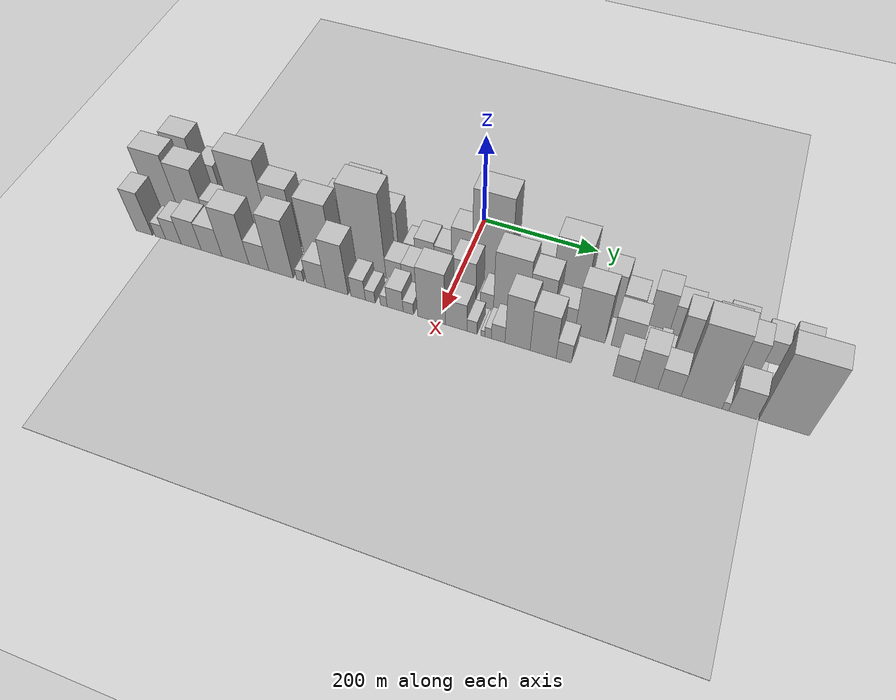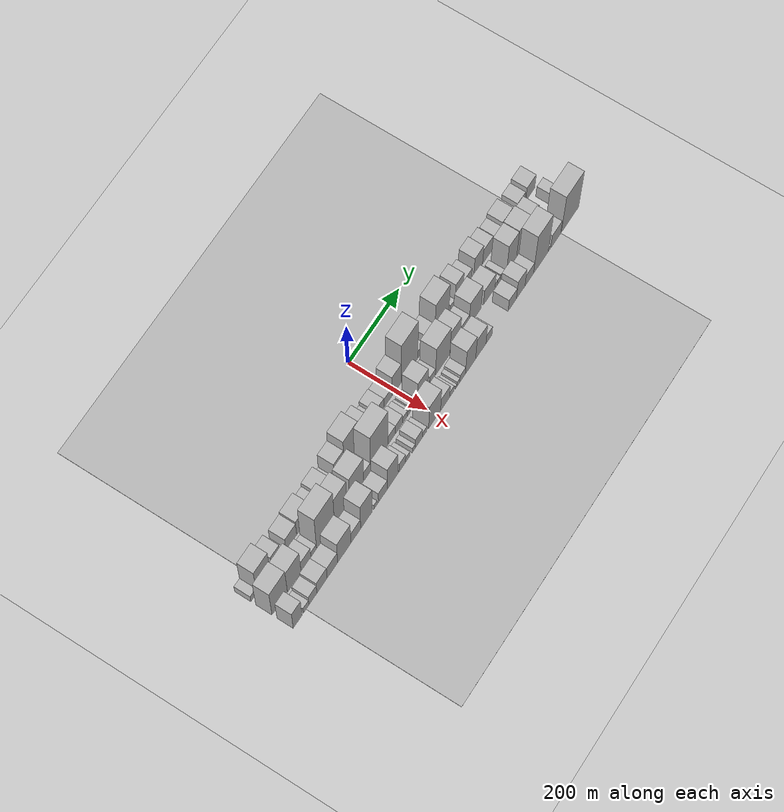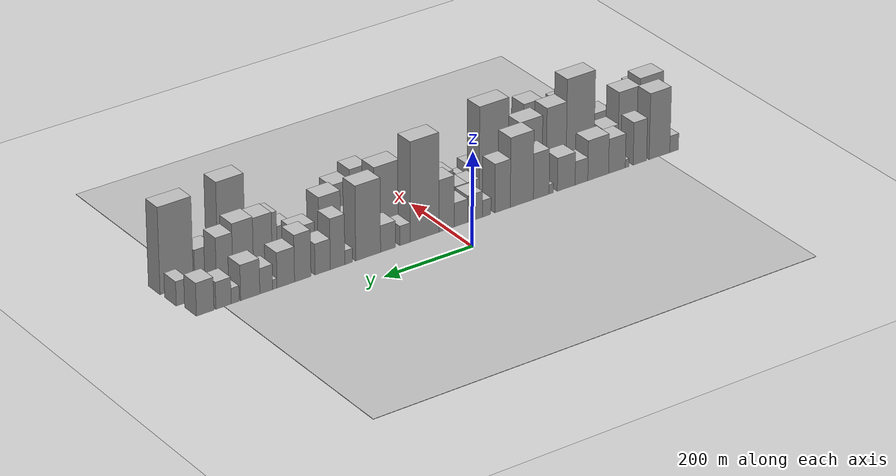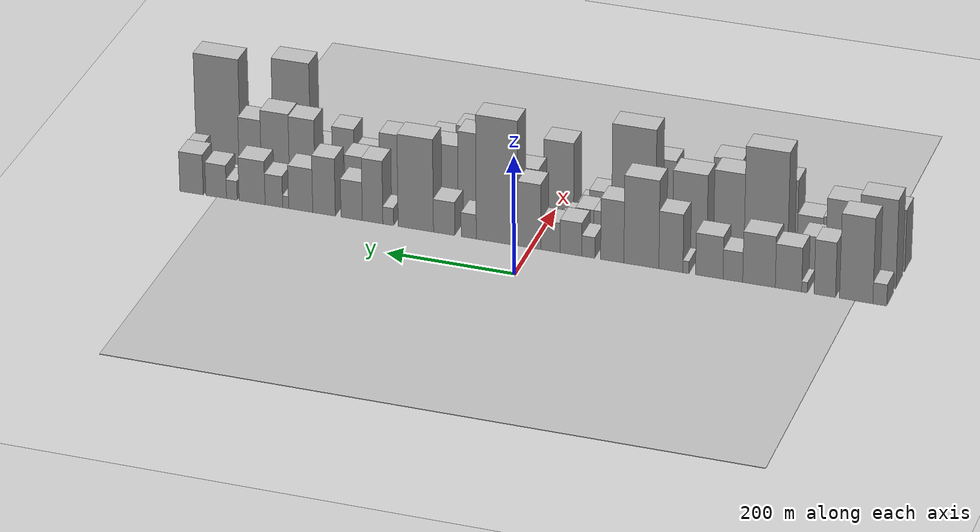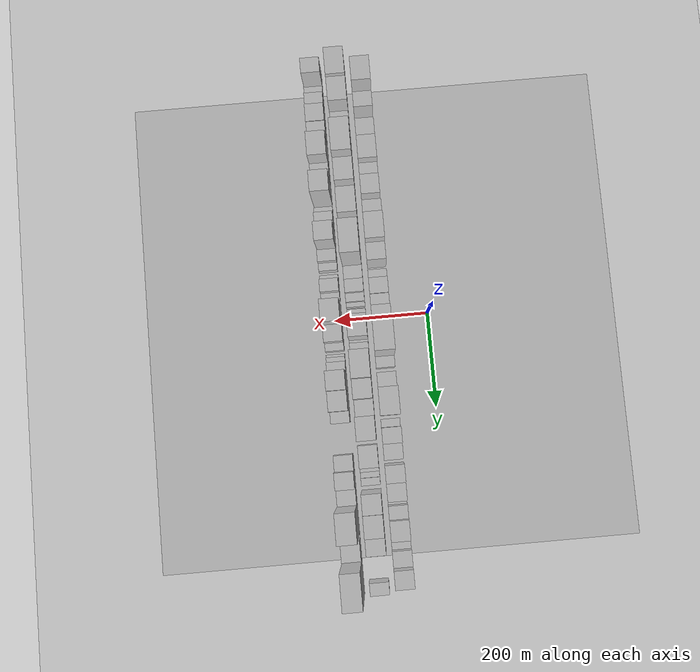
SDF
<?xml version="1.0" encoding="utf-8"?>

<sdf version="1.6">

   <world name="default">

      <gui fullscreen="0">

         <camera name="user_camera">

            <pose>-15 0 4.57585 0 0 0</pose>

            <view_controller>orbit</view_controller>

         </camera>

      </gui>

      <scene>

         <sky>

           <clouds>

             <speed>12</speed>

           </clouds>

         </sky>

         <ambient>0.4 0.4 0.4 1</ambient>

         <background>0.7 0.7 0.7 1</background>

         <shadows>1</shadows>

      </scene>

      <gravity>0 0 -9.8066</gravity>

      <magnetic_field>6e-06 2.3e-05 -4.2e-05</magnetic_field>

      <physics default="0" name="default_physics" type="ode">

         <ode>

            <solver>

               <type>quick</type>

               <iters>10</iters>

               <sor>1.0</sor>

               <use_dynamic_moi_rescaling>0</use_dynamic_moi_rescaling>

            </solver>

            <constraints>

               <cfm>0</cfm>

               <erp>0.2</erp>

               <contact_max_correcting_vel>100</contact_max_correcting_vel>

               <contact_surface_layer>0.001</contact_surface_layer>

            </constraints>

         </ode>

         <max_step_size>0.004</max_step_size>

         <real_time_factor>1</real_time_factor>

         <real_time_update_rate>250</real_time_update_rate>

      </physics>

      <light name="sun" type="directional">

         <cast_shadows>1</cast_shadows>

         <pose>0 0 10 0 0 0</pose>

         <diffuse>0.8 0.8 0.8 1</diffuse>

         <specular>0.2 0.2 0.2 1</specular>

         <attenuation>

            <range>1000</range>

            <constant>0.9</constant>

            <linear>0.01</linear>

            <quadratic>0.001</quadratic>

         </attenuation>

         <direction>-0.5 0.1 -0.9</direction>

      </light>

      <include>

         <name>ground_plane_1</name>

         <uri>model://HANNAS_ground_plane</uri>

         <pose>0 0 0  0 0 0</pose>

      </include>

      <include>

         <name>ground_plane_2</name>

         <uri>model://HANNAS_ground_plane</uri>

         <pose>100 0 0  0 0 0</pose>

      </include>

      <model name="building_1">

         <static>1</static>

         <pose frame="">100.0000 -537.4205 0 0.000000 0.000000 0.000000</pose>

         <link name="link">

            <pose frame="">0 0 18.00 0 0 0</pose>

            <collision name="collision">

               <geometry>

                  <box>

                     <size>40.0000 21.1590 36.0000</size>

                  </box>

               </geometry>

               <max_contacts>10</max_contacts>

               <surface>

                  <contact>

                     <ode/>

                  </contact>

                  <bounce/>

                  <friction>

                     <torsional>

                        <ode/>

                     </torsional>

                     <ode/>

                  </friction>

               </surface>

            </collision>

            <visual name="visual">

               <cast_shadows>0</cast_shadows>

               <geometry>

                  <box>

                     <size>40.0000 21.1590 36.0000</size>

                  </box>

               </geometry>

               <material>

                  <script>

                     <uri>model://HANNAS_wall/materials/scripts</uri>

                     <uri>model://HANNAS_wall/materials/textures</uri>

                     <name>vrc/HANNAS_wall</name>

                  </script>

               </material>

            </visual>

            <self_collide>0</self_collide>

            <enable_wind>0</enable_wind>

            <kinematic>0</kinematic>

         </link>

      </model>

      <model name="building_2">

         <static>1</static>

         <pose frame="">100.0000 -501.5422 0 0.000000 0.000000 0.000000</pose>

         <link name="link">

            <pose frame="">0 0 72.00 0 0 0</pose>

            <collision name="collision">

               <geometry>

                  <box>

                     <size>40.0000 50.5977 144.0000</size>

                  </box>

               </geometry>

               <max_contacts>10</max_contacts>

               <surface>

                  <contact>

                     <ode/>

                  </contact>

                  <bounce/>

                  <friction>

                     <torsional>

                        <ode/>

                     </torsional>

                     <ode/>

                  </friction>

               </surface>

            </collision>

            <visual name="visual">

               <cast_shadows>0</cast_shadows>

               <geometry>

                  <box>

                     <size>40.0000 50.5977 144.0000</size>

                  </box>

               </geometry>

               <material>

                  <script>

                     <uri>model://HANNAS_wall/materials/scripts</uri>

                     <uri>model://HANNAS_wall/materials/textures</uri>

                     <name>vrc/HANNAS_wall</name>

                  </script>

               </material>

            </visual>

            <self_collide>0</self_collide>

            <enable_wind>0</enable_wind>

            <kinematic>0</kinematic>

         </link>

      </model>

      <model name="building_3">

         <static>1</static>

         <pose frame="">100.0000 -453.8907 0 0.000000 0.000000 0.000000</pose>

         <link name="link">

            <pose frame="">0 0 46.50 0 0 0</pose>

            <collision name="collision">

               <geometry>

                  <box>

                     <size>40.0000 32.7053 93.0000</size>

                  </box>

               </geometry>

               <max_contacts>10</max_contacts>

               <surface>

                  <contact>

                     <ode/>

                  </contact>

                  <bounce/>

                  <friction>

                     <torsional>

                        <ode/>

                     </torsional>

                     <ode/>

                  </friction>

               </surface>

            </collision>

            <visual name="visual">

               <cast_shadows>0</cast_shadows>

               <geometry>

                  <box>

                     <size>40.0000 32.7053 93.0000</size>

                  </box>

               </geometry>

               <material>

                  <script>

                     <uri>model://HANNAS_wall/materials/scripts</uri>

                     <uri>model://HANNAS_wall/materials/textures</uri>

                     <name>vrc/HANNAS_wall</name>

                  </script>

               </material>

            </visual>

            <self_collide>0</self_collide>

            <enable_wind>0</enable_wind>

            <kinematic>0</kinematic>

         </link>

      </model>

      <model name="building_4">

         <static>1</static>

         <pose frame="">100.0000 -423.0930 0 0.000000 0.000000 0.000000</pose>

         <link name="link">

            <pose frame="">0 0 9.00 0 0 0</pose>

            <collision name="collision">

               <geometry>

                  <box>

                     <size>40.0000 8.8902 18.0000</size>

                  </box>

               </geometry>

               <max_contacts>10</max_contacts>

               <surface>

                  <contact>

                     <ode/>

                  </contact>

                  <bounce/>

                  <friction>

                     <torsional>

                        <ode/>

                     </torsional>

                     <ode/>

                  </friction>

               </surface>

            </collision>

            <visual name="visual">

               <cast_shadows>0</cast_shadows>

               <geometry>

                  <box>

                     <size>40.0000 8.8902 18.0000</size>

                  </box>

               </geometry>

               <material>

                  <script>

                     <uri>model://HANNAS_wall/materials/scripts</uri>

                     <uri>model://HANNAS_wall/materials/textures</uri>

                     <name>vrc/HANNAS_wall</name>

                  </script>

               </material>

            </visual>

            <self_collide>0</self_collide>

            <enable_wind>0</enable_wind>

            <kinematic>0</kinematic>

         </link>

      </model>

      <model name="building_5">

         <static>1</static>

         <pose frame="">100.0000 -398.4625 0 0.000000 0.000000 0.000000</pose>

         <link name="link">

            <pose frame="">0 0 37.50 0 0 0</pose>

            <collision name="collision">

               <geometry>

                  <box>

                     <size>40.0000 40.3708 75.0000</size>

                  </box>

               </geometry>

               <max_contacts>10</max_contacts>

               <surface>

                  <contact>

                     <ode/>

                  </contact>

                  <bounce/>

                  <friction>

                     <torsional>

                        <ode/>

                     </torsional>

                     <ode/>

                  </friction>

               </surface>

            </collision>

            <visual name="visual">

               <cast_shadows>0</cast_shadows>

               <geometry>

                  <box>

                     <size>40.0000 40.3708 75.0000</size>

                  </box>

               </geometry>

               <material>

                  <script>

                     <uri>model://HANNAS_wall/materials/scripts</uri>

                     <uri>model://HANNAS_wall/materials/textures</uri>

                     <name>vrc/HANNAS_wall</name>

                  </script>

               </material>

            </visual>

            <self_collide>0</self_collide>

            <enable_wind>0</enable_wind>

            <kinematic>0</kinematic>

         </link>

      </model>

      <model name="building_6">

         <static>1</static>

         <pose frame="">100.0000 -353.3126 0 0.000000 0.000000 0.000000</pose>

         <link name="link">

            <pose frame="">0 0 43.50 0 0 0</pose>

            <collision name="collision">

               <geometry>

                  <box>

                     <size>40.0000 49.9289 87.0000</size>

                  </box>

               </geometry>

               <max_contacts>10</max_contacts>

               <surface>

                  <contact>

                     <ode/>

                  </contact>

                  <bounce/>

                  <friction>

                     <torsional>

                        <ode/>

                     </torsional>

                     <ode/>

                  </friction>

               </surface>

            </collision>

            <visual name="visual">

               <cast_shadows>0</cast_shadows>

               <geometry>

                  <box>

                     <size>40.0000 49.9289 87.0000</size>

                  </box>

               </geometry>

               <material>

                  <script>

                     <uri>model://HANNAS_wall/materials/scripts</uri>

                     <uri>model://HANNAS_wall/materials/textures</uri>

                     <name>vrc/HANNAS_wall</name>

                  </script>

               </material>

            </visual>

            <self_collide>0</self_collide>

            <enable_wind>0</enable_wind>

            <kinematic>0</kinematic>

         </link>

      </model>

      <model name="building_7">

         <static>1</static>

         <pose frame="">100.0000 -313.2135 0 0.000000 0.000000 0.000000</pose>

         <link name="link">

            <pose frame="">0 0 25.50 0 0 0</pose>

            <collision name="collision">

               <geometry>

                  <box>

                     <size>40.0000 30.2694 51.0000</size>

                  </box>

               </geometry>

               <max_contacts>10</max_contacts>

               <surface>

                  <contact>

                     <ode/>

                  </contact>

                  <bounce/>

                  <friction>

                     <torsional>

                        <ode/>

                     </torsional>

                     <ode/>

                  </friction>

               </surface>

            </collision>

            <visual name="visual">

               <cast_shadows>0</cast_shadows>

               <geometry>

                  <box>

                     <size>40.0000 30.2694 51.0000</size>

                  </box>

               </geometry>

               <material>

                  <script>

                     <uri>model://HANNAS_wall/materials/scripts</uri>

                     <uri>model://HANNAS_wall/materials/textures</uri>

                     <name>vrc/HANNAS_wall</name>

                  </script>

               </material>

            </visual>

            <self_collide>0</self_collide>

            <enable_wind>0</enable_wind>

            <kinematic>0</kinematic>

         </link>

      </model>

      <model name="building_8">

         <static>1</static>

         <pose frame="">100.0000 -276.9280 0 0.000000 0.000000 0.000000</pose>

         <link name="link">

            <pose frame="">0 0 36.00 0 0 0</pose>

            <collision name="collision">

               <geometry>

                  <box>

                     <size>40.0000 42.3017 72.0000</size>

                  </box>

               </geometry>

               <max_contacts>10</max_contacts>

               <surface>

                  <contact>

                     <ode/>

                  </contact>

                  <bounce/>

                  <friction>

                     <torsional>

                        <ode/>

                     </torsional>

                     <ode/>

                  </friction>

               </surface>

            </collision>

            <visual name="visual">

               <cast_shadows>0</cast_shadows>

               <geometry>

                  <box>

                     <size>40.0000 42.3017 72.0000</size>

                  </box>

               </geometry>

               <material>

                  <script>

                     <uri>model://HANNAS_wall/materials/scripts</uri>

                     <uri>model://HANNAS_wall/materials/textures</uri>

                     <name>vrc/HANNAS_wall</name>

                  </script>

               </material>

            </visual>

            <self_collide>0</self_collide>

            <enable_wind>0</enable_wind>

            <kinematic>0</kinematic>

         </link>

      </model>

      <model name="building_9">

         <static>1</static>

         <pose frame="">100.0000 -241.0369 0 0.000000 0.000000 0.000000</pose>

         <link name="link">

            <pose frame="">0 0 10.50 0 0 0</pose>

            <collision name="collision">

               <geometry>

                  <box>

                     <size>40.0000 9.4805 21.0000</size>

                  </box>

               </geometry>

               <max_contacts>10</max_contacts>

               <surface>

                  <contact>

                     <ode/>

                  </contact>

                  <bounce/>

                  <friction>

                     <torsional>

                        <ode/>

                     </torsional>

                     <ode/>

                  </friction>

               </surface>

            </collision>

            <visual name="visual">

               <cast_shadows>0</cast_shadows>

               <geometry>

                  <box>

                     <size>40.0000 9.4805 21.0000</size>

                  </box>

               </geometry>

               <material>

                  <script>

                     <uri>model://HANNAS_wall/materials/scripts</uri>

                     <uri>model://HANNAS_wall/materials/textures</uri>

                     <name>vrc/HANNAS_wall</name>

                  </script>

               </material>

            </visual>

            <self_collide>0</self_collide>

            <enable_wind>0</enable_wind>

            <kinematic>0</kinematic>

         </link>

      </model>

      <model name="building_10">

         <static>1</static>

         <pose frame="">100.0000 -217.7313 0 0.000000 0.000000 0.000000</pose>

         <link name="link">

            <pose frame="">0 0 49.50 0 0 0</pose>

            <collision name="collision">

               <geometry>

                  <box>

                     <size>40.0000 37.1306 99.0000</size>

                  </box>

               </geometry>

               <max_contacts>10</max_contacts>

               <surface>

                  <contact>

                     <ode/>

                  </contact>

                  <bounce/>

                  <friction>

                     <torsional>

                        <ode/>

                     </torsional>

                     <ode/>

                  </friction>

               </surface>

            </collision>

            <visual name="visual">

               <cast_shadows>0</cast_shadows>

               <geometry>

                  <box>

                     <size>40.0000 37.1306 99.0000</size>

                  </box>

               </geometry>

               <material>

                  <script>

                     <uri>model://HANNAS_wall/materials/scripts</uri>

                     <uri>model://HANNAS_wall/materials/textures</uri>

                     <name>vrc/HANNAS_wall</name>

                  </script>

               </material>

            </visual>

            <self_collide>0</self_collide>

            <enable_wind>0</enable_wind>

            <kinematic>0</kinematic>

         </link>

      </model>

      <model name="building_11">

         <static>1</static>

         <pose frame="">100.0000 -172.0559 0 0.000000 0.000000 0.000000</pose>

         <link name="link">

            <pose frame="">0 0 75.00 0 0 0</pose>

            <collision name="collision">

               <geometry>

                  <box>

                     <size>40.0000 54.2202 150.0000</size>

                  </box>

               </geometry>

               <max_contacts>10</max_contacts>

               <surface>

                  <contact>

                     <ode/>

                  </contact>

                  <bounce/>

                  <friction>

                     <torsional>

                        <ode/>

                     </torsional>

                     <ode/>

                  </friction>

               </surface>

            </collision>

            <visual name="visual">

               <cast_shadows>0</cast_shadows>

               <geometry>

                  <box>

                     <size>40.0000 54.2202 150.0000</size>

                  </box>

               </geometry>

               <material>

                  <script>

                     <uri>model://HANNAS_wall/materials/scripts</uri>

                     <uri>model://HANNAS_wall/materials/textures</uri>

                     <name>vrc/HANNAS_wall</name>

                  </script>

               </material>

            </visual>

            <self_collide>0</self_collide>

            <enable_wind>0</enable_wind>

            <kinematic>0</kinematic>

         </link>

      </model>

      <model name="building_12">

         <static>1</static>

         <pose frame="">100.0000 -126.8319 0 0.000000 0.000000 0.000000</pose>

         <link name="link">

            <pose frame="">0 0 52.50 0 0 0</pose>

            <collision name="collision">

               <geometry>

                  <box>

                     <size>40.0000 36.2277 105.0000</size>

                  </box>

               </geometry>

               <max_contacts>10</max_contacts>

               <surface>

                  <contact>

                     <ode/>

                  </contact>

                  <bounce/>

                  <friction>

                     <torsional>

                        <ode/>

                     </torsional>

                     <ode/>

                  </friction>

               </surface>

            </collision>

            <visual name="visual">

               <cast_shadows>0</cast_shadows>

               <geometry>

                  <box>

                     <size>40.0000 36.2277 105.0000</size>

                  </box>

               </geometry>

               <material>

                  <script>

                     <uri>model://HANNAS_wall/materials/scripts</uri>

                     <uri>model://HANNAS_wall/materials/textures</uri>

                     <name>vrc/HANNAS_wall</name>

                  </script>

               </material>

            </visual>

            <self_collide>0</self_collide>

            <enable_wind>0</enable_wind>

            <kinematic>0</kinematic>

         </link>

      </model>

      <model name="building_13">

         <static>1</static>

         <pose frame="">100.0000 -89.6416 0 0.000000 0.000000 0.000000</pose>

         <link name="link">

            <pose frame="">0 0 18.00 0 0 0</pose>

            <collision name="collision">

               <geometry>

                  <box>

                     <size>40.0000 20.1530 36.0000</size>

                  </box>

               </geometry>

               <max_contacts>10</max_contacts>

               <surface>

                  <contact>

                     <ode/>

                  </contact>

                  <bounce/>

                  <friction>

                     <torsional>

                        <ode/>

                     </torsional>

                     <ode/>

                  </friction>

               </surface>

            </collision>

            <visual name="visual">

               <cast_shadows>0</cast_shadows>

               <geometry>

                  <box>

                     <size>40.0000 20.1530 36.0000</size>

                  </box>

               </geometry>

               <material>

                  <script>

                     <uri>model://HANNAS_wall/materials/scripts</uri>

                     <uri>model://HANNAS_wall/materials/textures</uri>

                     <name>vrc/HANNAS_wall</name>

                  </script>

               </material>

            </visual>

            <self_collide>0</self_collide>

            <enable_wind>0</enable_wind>

            <kinematic>0</kinematic>

         </link>

      </model>

      <model name="building_14">

         <static>1</static>

         <pose frame="">100.0000 -62.5326 0 0.000000 0.000000 0.000000</pose>

         <link name="link">

            <pose frame="">0 0 28.50 0 0 0</pose>

            <collision name="collision">

               <geometry>

                  <box>

                     <size>40.0000 34.0651 57.0000</size>

                  </box>

               </geometry>

               <max_contacts>10</max_contacts>

               <surface>

                  <contact>

                     <ode/>

                  </contact>

                  <bounce/>

                  <friction>

                     <torsional>

                        <ode/>

                     </torsional>

                     <ode/>

                  </friction>

               </surface>

            </collision>

            <visual name="visual">

               <cast_shadows>0</cast_shadows>

               <geometry>

                  <box>

                     <size>40.0000 34.0651 57.0000</size>

                  </box>

               </geometry>

               <material>

                  <script>

                     <uri>model://HANNAS_wall/materials/scripts</uri>

                     <uri>model://HANNAS_wall/materials/textures</uri>

                     <name>vrc/HANNAS_wall</name>

                  </script>

               </material>

            </visual>

            <self_collide>0</self_collide>

            <enable_wind>0</enable_wind>

            <kinematic>0</kinematic>

         </link>

      </model>

      <model name="building_15">

         <static>1</static>

         <pose frame="">100.0000 -30.2260 0 0.000000 0.000000 0.000000</pose>

         <link name="link">

            <pose frame="">0 0 25.50 0 0 0</pose>

            <collision name="collision">

               <geometry>

                  <box>

                     <size>40.0000 30.5481 51.0000</size>

                  </box>

               </geometry>

               <max_contacts>10</max_contacts>

               <surface>

                  <contact>

                     <ode/>

                  </contact>

                  <bounce/>

                  <friction>

                     <torsional>

                        <ode/>

                     </torsional>

                     <ode/>

                  </friction>

               </surface>

            </collision>

            <visual name="visual">

               <cast_shadows>0</cast_shadows>

               <geometry>

                  <box>

                     <size>40.0000 30.5481 51.0000</size>

                  </box>

               </geometry>

               <material>

                  <script>

                     <uri>model://HANNAS_wall/materials/scripts</uri>

                     <uri>model://HANNAS_wall/materials/textures</uri>

                     <name>vrc/HANNAS_wall</name>

                  </script>

               </material>

            </visual>

            <self_collide>0</self_collide>

            <enable_wind>0</enable_wind>

            <kinematic>0</kinematic>

         </link>

      </model>

      <model name="building_16">

         <static>1</static>

         <pose frame="">100.0000 3.0005 0 0.000000 0.000000 0.000000</pose>

         <link name="link">

            <pose frame="">0 0 55.50 0 0 0</pose>

            <collision name="collision">

               <geometry>

                  <box>

                     <size>40.0000 35.9050 111.0000</size>

                  </box>

               </geometry>

               <max_contacts>10</max_contacts>

               <surface>

                  <contact>

                     <ode/>

                  </contact>

                  <bounce/>

                  <friction>

                     <torsional>

                        <ode/>

                     </torsional>

                     <ode/>

                  </friction>

               </surface>

            </collision>

            <visual name="visual">

               <cast_shadows>0</cast_shadows>

               <geometry>

                  <box>

                     <size>40.0000 35.9050 111.0000</size>

                  </box>

               </geometry>

               <material>

                  <script>

                     <uri>model://HANNAS_wall/materials/scripts</uri>

                     <uri>model://HANNAS_wall/materials/textures</uri>

                     <name>vrc/HANNAS_wall</name>

                  </script>

               </material>

            </visual>

            <self_collide>0</self_collide>

            <enable_wind>0</enable_wind>

            <kinematic>0</kinematic>

         </link>

      </model>

      <model name="building_17">

         <static>1</static>

         <pose frame="">100.0000 53.5414 0 0.000000 0.000000 0.000000</pose>

         <link name="link">

            <pose frame="">0 0 106.50 0 0 0</pose>

            <collision name="collision">

               <geometry>

                  <box>

                     <size>40.0000 65.1768 213.0000</size>

                  </box>

               </geometry>

               <max_contacts>10</max_contacts>

               <surface>

                  <contact>

                     <ode/>

                  </contact>

                  <bounce/>

                  <friction>

                     <torsional>

                        <ode/>

                     </torsional>

                     <ode/>

                  </friction>

               </surface>

            </collision>

            <visual name="visual">

               <cast_shadows>0</cast_shadows>

               <geometry>

                  <box>

                     <size>40.0000 65.1768 213.0000</size>

                  </box>

               </geometry>

               <material>

                  <script>

                     <uri>model://HANNAS_wall/materials/scripts</uri>

                     <uri>model://HANNAS_wall/materials/textures</uri>

                     <name>vrc/HANNAS_wall</name>

                  </script>

               </material>

            </visual>

            <self_collide>0</self_collide>

            <enable_wind>0</enable_wind>

            <kinematic>0</kinematic>

         </link>

      </model>

      <model name="building_18">

         <static>1</static>

         <pose frame="">100.0000 98.0382 0 0.000000 0.000000 0.000000</pose>

         <link name="link">

            <pose frame="">0 0 21.00 0 0 0</pose>

            <collision name="collision">

               <geometry>

                  <box>

                     <size>40.0000 23.8167 42.0000</size>

                  </box>

               </geometry>

               <max_contacts>10</max_contacts>

               <surface>

                  <contact>

                     <ode/>

                  </contact>

                  <bounce/>

                  <friction>

                     <torsional>

                        <ode/>

                     </torsional>

                     <ode/>

                  </friction>

               </surface>

            </collision>

            <visual name="visual">

               <cast_shadows>0</cast_shadows>

               <geometry>

                  <box>

                     <size>40.0000 23.8167 42.0000</size>

                  </box>

               </geometry>

               <material>

                  <script>

                     <uri>model://HANNAS_wall/materials/scripts</uri>

                     <uri>model://HANNAS_wall/materials/textures</uri>

                     <name>vrc/HANNAS_wall</name>

                  </script>

               </material>

            </visual>

            <self_collide>0</self_collide>

            <enable_wind>0</enable_wind>

            <kinematic>0</kinematic>

         </link>

      </model>

      <model name="building_19">

         <static>1</static>

         <pose frame="">100.0000 136.8431 0 0.000000 0.000000 0.000000</pose>

         <link name="link">

            <pose frame="">0 0 28.50 0 0 0</pose>

            <collision name="collision">

               <geometry>

                  <box>

                     <size>40.0000 33.7931 57.0000</size>

                  </box>

               </geometry>

               <max_contacts>10</max_contacts>

               <surface>

                  <contact>

                     <ode/>

                  </contact>

                  <bounce/>

                  <friction>

                     <torsional>

                        <ode/>

                     </torsional>

                     <ode/>

                  </friction>

               </surface>

            </collision>

            <visual name="visual">

               <cast_shadows>0</cast_shadows>

               <geometry>

                  <box>

                     <size>40.0000 33.7931 57.0000</size>

                  </box>

               </geometry>

               <material>

                  <script>

                     <uri>model://HANNAS_wall/materials/scripts</uri>

                     <uri>model://HANNAS_wall/materials/textures</uri>

                     <name>vrc/HANNAS_wall</name>

                  </script>

               </material>

            </visual>

            <self_collide>0</self_collide>

            <enable_wind>0</enable_wind>

            <kinematic>0</kinematic>

         </link>

      </model>

      <model name="building_20">

         <static>1</static>

         <pose frame="">100.0000 181.7698 0 0.000000 0.000000 0.000000</pose>

         <link name="link">

            <pose frame="">0 0 79.50 0 0 0</pose>

            <collision name="collision">

               <geometry>

                  <box>

                     <size>40.0000 56.0602 159.0000</size>

                  </box>

               </geometry>

               <max_contacts>10</max_contacts>

               <surface>

                  <contact>

                     <ode/>

                  </contact>

                  <bounce/>

                  <friction>

                     <torsional>

                        <ode/>

                     </torsional>

                     <ode/>

                  </friction>

               </surface>

            </collision>

            <visual name="visual">

               <cast_shadows>0</cast_shadows>

               <geometry>

                  <box>

                     <size>40.0000 56.0602 159.0000</size>

                  </box>

               </geometry>

               <material>

                  <script>

                     <uri>model://HANNAS_wall/materials/scripts</uri>

                     <uri>model://HANNAS_wall/materials/textures</uri>

                     <name>vrc/HANNAS_wall</name>

                  </script>

               </material>

            </visual>

            <self_collide>0</self_collide>

            <enable_wind>0</enable_wind>

            <kinematic>0</kinematic>

         </link>

      </model>

      <model name="building_21">

         <static>1</static>

         <pose frame="">100.0000 225.4258 0 0.000000 0.000000 0.000000</pose>

         <link name="link">

            <pose frame="">0 0 15.00 0 0 0</pose>

            <collision name="collision">

               <geometry>

                  <box>

                     <size>40.0000 17.2519 30.0000</size>

                  </box>

               </geometry>

               <max_contacts>10</max_contacts>

               <surface>

                  <contact>

                     <ode/>

                  </contact>

                  <bounce/>

                  <friction>

                     <torsional>

                        <ode/>

                     </torsional>

                     <ode/>

                  </friction>

               </surface>

            </collision>

            <visual name="visual">

               <cast_shadows>0</cast_shadows>

               <geometry>

                  <box>

                     <size>40.0000 17.2519 30.0000</size>

                  </box>

               </geometry>

               <material>

                  <script>

                     <uri>model://HANNAS_wall/materials/scripts</uri>

                     <uri>model://HANNAS_wall/materials/textures</uri>

                     <name>vrc/HANNAS_wall</name>

                  </script>

               </material>

            </visual>

            <self_collide>0</self_collide>

            <enable_wind>0</enable_wind>

            <kinematic>0</kinematic>

         </link>

      </model>

      <model name="building_22">

         <static>1</static>

         <pose frame="">100.0000 250.4001 0 0.000000 0.000000 0.000000</pose>

         <link name="link">

            <pose frame="">0 0 54.00 0 0 0</pose>

            <collision name="collision">

               <geometry>

                  <box>

                     <size>40.0000 32.6967 108.0000</size>

                  </box>

               </geometry>

               <max_contacts>10</max_contacts>

               <surface>

                  <contact>

                     <ode/>

                  </contact>

                  <bounce/>

                  <friction>

                     <torsional>

                        <ode/>

                     </torsional>

                     <ode/>

                  </friction>

               </surface>

            </collision>

            <visual name="visual">

               <cast_shadows>0</cast_shadows>

               <geometry>

                  <box>

                     <size>40.0000 32.6967 108.0000</size>

                  </box>

               </geometry>

               <material>

                  <script>

                     <uri>model://HANNAS_wall/materials/scripts</uri>

                     <uri>model://HANNAS_wall/materials/textures</uri>

                     <name>vrc/HANNAS_wall</name>

                  </script>

               </material>

            </visual>

            <self_collide>0</self_collide>

            <enable_wind>0</enable_wind>

            <kinematic>0</kinematic>

         </link>

      </model>

      <model name="building_23">

         <static>1</static>

         <pose frame="">100.0000 283.7714 0 0.000000 0.000000 0.000000</pose>

         <link name="link">

            <pose frame="">0 0 33.00 0 0 0</pose>

            <collision name="collision">

               <geometry>

                  <box>

                     <size>40.0000 34.0458 66.0000</size>

                  </box>

               </geometry>

               <max_contacts>10</max_contacts>

               <surface>

                  <contact>

                     <ode/>

                  </contact>

                  <bounce/>

                  <friction>

                     <torsional>

                        <ode/>

                     </torsional>

                     <ode/>

                  </friction>

               </surface>

            </collision>

            <visual name="visual">

               <cast_shadows>0</cast_shadows>

               <geometry>

                  <box>

                     <size>40.0000 34.0458 66.0000</size>

                  </box>

               </geometry>

               <material>

                  <script>

                     <uri>model://HANNAS_wall/materials/scripts</uri>

                     <uri>model://HANNAS_wall/materials/textures</uri>

                     <name>vrc/HANNAS_wall</name>

                  </script>

               </material>

            </visual>

            <self_collide>0</self_collide>

            <enable_wind>0</enable_wind>

            <kinematic>0</kinematic>

         </link>

      </model>

      <model name="building_24">

         <static>1</static>

         <pose frame="">100.0000 327.9135 0 0.000000 0.000000 0.000000</pose>

         <link name="link">

            <pose frame="">0 0 49.50 0 0 0</pose>

            <collision name="collision">

               <geometry>

                  <box>

                     <size>40.0000 36.2383 99.0000</size>

                  </box>

               </geometry>

               <max_contacts>10</max_contacts>

               <surface>

                  <contact>

                     <ode/>

                  </contact>

                  <bounce/>

                  <friction>

                     <torsional>

                        <ode/>

                     </torsional>

                     <ode/>

                  </friction>

               </surface>

            </collision>

            <visual name="visual">

               <cast_shadows>0</cast_shadows>

               <geometry>

                  <box>

                     <size>40.0000 36.2383 99.0000</size>

                  </box>

               </geometry>

               <material>

                  <script>

                     <uri>model://HANNAS_wall/materials/scripts</uri>

                     <uri>model://HANNAS_wall/materials/textures</uri>

                     <name>vrc/HANNAS_wall</name>

                  </script>

               </material>

            </visual>

            <self_collide>0</self_collide>

            <enable_wind>0</enable_wind>

            <kinematic>0</kinematic>

         </link>

      </model>

      <model name="building_25">

         <static>1</static>

         <pose frame="">100.0000 365.3858 0 0.000000 0.000000 0.000000</pose>

         <link name="link">

            <pose frame="">0 0 37.50 0 0 0</pose>

            <collision name="collision">

               <geometry>

                  <box>

                     <size>40.0000 38.7064 75.0000</size>

                  </box>

               </geometry>

               <max_contacts>10</max_contacts>

               <surface>

                  <contact>

                     <ode/>

                  </contact>

                  <bounce/>

                  <friction>

                     <torsional>

                        <ode/>

                     </torsional>

                     <ode/>

                  </friction>

               </surface>

            </collision>

            <visual name="visual">

               <cast_shadows>0</cast_shadows>

               <geometry>

                  <box>

                     <size>40.0000 38.7064 75.0000</size>

                  </box>

               </geometry>

               <material>

                  <script>

                     <uri>model://HANNAS_wall/materials/scripts</uri>

                     <uri>model://HANNAS_wall/materials/textures</uri>

                     <name>vrc/HANNAS_wall</name>

                  </script>

               </material>

            </visual>

            <self_collide>0</self_collide>

            <enable_wind>0</enable_wind>

            <kinematic>0</kinematic>

         </link>

      </model>

      <model name="building_26">

         <static>1</static>

         <pose frame="">100.0000 389.5115 0 0.000000 0.000000 0.000000</pose>

         <link name="link">

            <pose frame="">0 0 10.50 0 0 0</pose>

            <collision name="collision">

               <geometry>

                  <box>

                     <size>40.0000 9.5450 21.0000</size>

                  </box>

               </geometry>

               <max_contacts>10</max_contacts>

               <surface>

                  <contact>

                     <ode/>

                  </contact>

                  <bounce/>

                  <friction>

                     <torsional>

                        <ode/>

                     </torsional>

                     <ode/>

                  </friction>

               </surface>

            </collision>

            <visual name="visual">

               <cast_shadows>0</cast_shadows>

               <geometry>

                  <box>

                     <size>40.0000 9.5450 21.0000</size>

                  </box>

               </geometry>

               <material>

                  <script>

                     <uri>model://HANNAS_wall/materials/scripts</uri>

                     <uri>model://HANNAS_wall/materials/textures</uri>

                     <name>vrc/HANNAS_wall</name>

                  </script>

               </material>

            </visual>

            <self_collide>0</self_collide>

            <enable_wind>0</enable_wind>

            <kinematic>0</kinematic>

         </link>

      </model>

      <model name="building_27">

         <static>1</static>

         <pose frame="">100.0000 408.4193 0 0.000000 0.000000 0.000000</pose>

         <link name="link">

            <pose frame="">0 0 27.00 0 0 0</pose>

            <collision name="collision">

               <geometry>

                  <box>

                     <size>40.0000 28.2707 54.0000</size>

                  </box>

               </geometry>

               <max_contacts>10</max_contacts>

               <surface>

                  <contact>

                     <ode/>

                  </contact>

                  <bounce/>

                  <friction>

                     <torsional>

                        <ode/>

                     </torsional>

                     <ode/>

                  </friction>

               </surface>

            </collision>

            <visual name="visual">

               <cast_shadows>0</cast_shadows>

               <geometry>

                  <box>

                     <size>40.0000 28.2707 54.0000</size>

                  </box>

               </geometry>

               <material>

                  <script>

                     <uri>model://HANNAS_wall/materials/scripts</uri>

                     <uri>model://HANNAS_wall/materials/textures</uri>

                     <name>vrc/HANNAS_wall</name>

                  </script>

               </material>

            </visual>

            <self_collide>0</self_collide>

            <enable_wind>0</enable_wind>

            <kinematic>0</kinematic>

         </link>

      </model>

      <model name="building_28">

         <static>1</static>

         <pose frame="">100.0000 443.5147 0 0.000000 0.000000 0.000000</pose>

         <link name="link">

            <pose frame="">0 0 37.50 0 0 0</pose>

            <collision name="collision">

               <geometry>

                  <box>

                     <size>40.0000 41.9201 75.0000</size>

                  </box>

               </geometry>

               <max_contacts>10</max_contacts>

               <surface>

                  <contact>

                     <ode/>

                  </contact>

                  <bounce/>

                  <friction>

                     <torsional>

                        <ode/>

                     </torsional>

                     <ode/>

                  </friction>

               </surface>

            </collision>

            <visual name="visual">

               <cast_shadows>0</cast_shadows>

               <geometry>

                  <box>

                     <size>40.0000 41.9201 75.0000</size>

                  </box>

               </geometry>

               <material>

                  <script>

                     <uri>model://HANNAS_wall/materials/scripts</uri>

                     <uri>model://HANNAS_wall/materials/textures</uri>

                     <name>vrc/HANNAS_wall</name>

                  </script>

               </material>

            </visual>

            <self_collide>0</self_collide>

            <enable_wind>0</enable_wind>

            <kinematic>0</kinematic>

         </link>

      </model>

      <model name="building_29">

         <static>1</static>

         <pose frame="">100.0000 476.2068 0 0.000000 0.000000 0.000000</pose>

         <link name="link">

            <pose frame="">0 0 16.50 0 0 0</pose>

            <collision name="collision">

               <geometry>

                  <box>

                     <size>40.0000 17.4642 33.0000</size>

                  </box>

               </geometry>

               <max_contacts>10</max_contacts>

               <surface>

                  <contact>

                     <ode/>

                  </contact>

                  <bounce/>

                  <friction>

                     <torsional>

                        <ode/>

                     </torsional>

                     <ode/>

                  </friction>

               </surface>

            </collision>

            <visual name="visual">

               <cast_shadows>0</cast_shadows>

               <geometry>

                  <box>

                     <size>40.0000 17.4642 33.0000</size>

                  </box>

               </geometry>

               <material>

                  <script>

                     <uri>model://HANNAS_wall/materials/scripts</uri>

                     <uri>model://HANNAS_wall/materials/textures</uri>

                     <name>vrc/HANNAS_wall</name>

                  </script>

               </material>

            </visual>

            <self_collide>0</self_collide>

            <enable_wind>0</enable_wind>

            <kinematic>0</kinematic>

         </link>

      </model>

      <model name="building_30">

         <static>1</static>

         <pose frame="">100.0000 501.6357 0 0.000000 0.000000 0.000000</pose>

         <link name="link">

            <pose frame="">0 0 28.50 0 0 0</pose>

            <collision name="collision">

               <geometry>

                  <box>

                     <size>40.0000 33.3936 57.0000</size>

                  </box>

               </geometry>

               <max_contacts>10</max_contacts>

               <surface>

                  <contact>

                     <ode/>

                  </contact>

                  <bounce/>

                  <friction>

                     <torsional>

                        <ode/>

                     </torsional>

                     <ode/>

                  </friction>

               </surface>

            </collision>

            <visual name="visual">

               <cast_shadows>0</cast_shadows>

               <geometry>

                  <box>

                     <size>40.0000 33.3936 57.0000</size>

                  </box>

               </geometry>

               <material>

                  <script>

                     <uri>model://HANNAS_wall/materials/scripts</uri>

                     <uri>model://HANNAS_wall/materials/textures</uri>

                     <name>vrc/HANNAS_wall</name>

                  </script>

               </material>

            </visual>

            <self_collide>0</self_collide>

            <enable_wind>0</enable_wind>

            <kinematic>0</kinematic>

         </link>

      </model>

      <model name="building_31">

         <static>1</static>

         <pose frame="">100.0000 541.3579 0 0.000000 0.000000 0.000000</pose>

         <link name="link">

            <pose frame="">0 0 34.50 0 0 0</pose>

            <collision name="collision">

               <geometry>

                  <box>

                     <size>40.0000 38.0507 69.0000</size>

                  </box>

               </geometry>

               <max_contacts>10</max_contacts>

               <surface>

                  <contact>

                     <ode/>

                  </contact>

                  <bounce/>

                  <friction>

                     <torsional>

                        <ode/>

                     </torsional>

                     <ode/>

                  </friction>

               </surface>

            </collision>

            <visual name="visual">

               <cast_shadows>0</cast_shadows>

               <geometry>

                  <box>

                     <size>40.0000 38.0507 69.0000</size>

                  </box>

               </geometry>

               <material>

                  <script>

                     <uri>model://HANNAS_wall/materials/scripts</uri>

                     <uri>model://HANNAS_wall/materials/textures</uri>

                     <name>vrc/HANNAS_wall</name>

                  </script>

               </material>

            </visual>

            <self_collide>0</self_collide>

            <enable_wind>0</enable_wind>

            <kinematic>0</kinematic>

         </link>

      </model>

      <model name="building_32">

         <static>1</static>

         <pose frame="">152.0000 -519.5265 0 0.000000 0.000000 0.000000</pose>

         <link name="link">

            <pose frame="">0 0 75.00 0 0 0</pose>

            <collision name="collision">

               <geometry>

                  <box>

                     <size>40.0000 56.9471 150.0000</size>

                  </box>

               </geometry>

               <max_contacts>10</max_contacts>

               <surface>

                  <contact>

                     <ode/>

                  </contact>

                  <bounce/>

                  <friction>

                     <torsional>

                        <ode/>

                     </torsional>

                     <ode/>

                  </friction>

               </surface>

            </collision>

            <visual name="visual">

               <cast_shadows>0</cast_shadows>

               <geometry>

                  <box>

                     <size>40.0000 56.9471 150.0000</size>

                  </box>

               </geometry>

               <material>

                  <script>

                     <uri>model://HANNAS_wall/materials/scripts</uri>

                     <uri>model://HANNAS_wall/materials/textures</uri>

                     <name>vrc/HANNAS_wall</name>

                  </script>

               </material>

            </visual>

            <self_collide>0</self_collide>

            <enable_wind>0</enable_wind>

            <kinematic>0</kinematic>

         </link>

      </model>

      <model name="building_33">

         <static>1</static>

         <pose frame="">152.0000 -465.7138 0 0.000000 0.000000 0.000000</pose>

         <link name="link">

            <pose frame="">0 0 67.50 0 0 0</pose>

            <collision name="collision">

               <geometry>

                  <box>

                     <size>40.0000 50.6783 135.0000</size>

                  </box>

               </geometry>

               <max_contacts>10</max_contacts>

               <surface>

                  <contact>

                     <ode/>

                  </contact>

                  <bounce/>

                  <friction>

                     <torsional>

                        <ode/>

                     </torsional>

                     <ode/>

                  </friction>

               </surface>

            </collision>

            <visual name="visual">

               <cast_shadows>0</cast_shadows>

               <geometry>

                  <box>

                     <size>40.0000 50.6783 135.0000</size>

                  </box>

               </geometry>

               <material>

                  <script>

                     <uri>model://HANNAS_wall/materials/scripts</uri>

                     <uri>model://HANNAS_wall/materials/textures</uri>

                     <name>vrc/HANNAS_wall</name>

                  </script>

               </material>

            </visual>

            <self_collide>0</self_collide>

            <enable_wind>0</enable_wind>

            <kinematic>0</kinematic>

         </link>

      </model>

      <model name="building_34">

         <static>1</static>

         <pose frame="">152.0000 -421.8914 0 0.000000 0.000000 0.000000</pose>

         <link name="link">

            <pose frame="">0 0 33.00 0 0 0</pose>

            <collision name="collision">

               <geometry>

                  <box>

                     <size>40.0000 36.9664 66.0000</size>

                  </box>

               </geometry>

               <max_contacts>10</max_contacts>

               <surface>

                  <contact>

                     <ode/>

                  </contact>

                  <bounce/>

                  <friction>

                     <torsional>

                        <ode/>

                     </torsional>

                     <ode/>

                  </friction>

               </surface>

            </collision>

            <visual name="visual">

               <cast_shadows>0</cast_shadows>

               <geometry>

                  <box>

                     <size>40.0000 36.9664 66.0000</size>

                  </box>

               </geometry>

               <material>

                  <script>

                     <uri>model://HANNAS_wall/materials/scripts</uri>

                     <uri>model://HANNAS_wall/materials/textures</uri>

                     <name>vrc/HANNAS_wall</name>

                  </script>

               </material>

            </visual>

            <self_collide>0</self_collide>

            <enable_wind>0</enable_wind>

            <kinematic>0</kinematic>

         </link>

      </model>

      <model name="building_35">

         <static>1</static>

         <pose frame="">152.0000 -392.8141 0 0.000000 0.000000 0.000000</pose>

         <link name="link">

            <pose frame="">0 0 18.00 0 0 0</pose>

            <collision name="collision">

               <geometry>

                  <box>

                     <size>40.0000 21.1882 36.0000</size>

                  </box>

               </geometry>

               <max_contacts>10</max_contacts>

               <surface>

                  <contact>

                     <ode/>

                  </contact>

                  <bounce/>

                  <friction>

                     <torsional>

                        <ode/>

                     </torsional>

                     <ode/>

                  </friction>

               </surface>

            </collision>

            <visual name="visual">

               <cast_shadows>0</cast_shadows>

               <geometry>

                  <box>

                     <size>40.0000 21.1882 36.0000</size>

                  </box>

               </geometry>

               <material>

                  <script>

                     <uri>model://HANNAS_wall/materials/scripts</uri>

                     <uri>model://HANNAS_wall/materials/textures</uri>

                     <name>vrc/HANNAS_wall</name>

                  </script>

               </material>

            </visual>

            <self_collide>0</self_collide>

            <enable_wind>0</enable_wind>

            <kinematic>0</kinematic>

         </link>

      </model>

      <model name="building_36">

         <static>1</static>

         <pose frame="">152.0000 -348.6404 0 0.000000 0.000000 0.000000</pose>

         <link name="link">

            <pose frame="">0 0 100.50 0 0 0</pose>

            <collision name="collision">

               <geometry>

                  <box>

                     <size>40.0000 67.1592 201.0000</size>

                  </box>

               </geometry>

               <max_contacts>10</max_contacts>

               <surface>

                  <contact>

                     <ode/>

                  </contact>

                  <bounce/>

                  <friction>

                     <torsional>

                        <ode/>

                     </torsional>

                     <ode/>

                  </friction>

               </surface>

            </collision>

            <visual name="visual">

               <cast_shadows>0</cast_shadows>

               <geometry>

                  <box>

                     <size>40.0000 67.1592 201.0000</size>

                  </box>

               </geometry>

               <material>

                  <script>

                     <uri>model://HANNAS_wall/materials/scripts</uri>

                     <uri>model://HANNAS_wall/materials/textures</uri>

                     <name>vrc/HANNAS_wall</name>

                  </script>

               </material>

            </visual>

            <self_collide>0</self_collide>

            <enable_wind>0</enable_wind>

            <kinematic>0</kinematic>

         </link>

      </model>

      <model name="building_37">

         <static>1</static>

         <pose frame="">152.0000 -291.4726 0 0.000000 0.000000 0.000000</pose>

         <link name="link">

            <pose frame="">0 0 76.50 0 0 0</pose>

            <collision name="collision">

               <geometry>

                  <box>

                     <size>40.0000 47.1764 153.0000</size>

                  </box>

               </geometry>

               <max_contacts>10</max_contacts>

               <surface>

                  <contact>

                     <ode/>

                  </contact>

                  <bounce/>

                  <friction>

                     <torsional>

                        <ode/>

                     </torsional>

                     <ode/>

                  </friction>

               </surface>

            </collision>

            <visual name="visual">

               <cast_shadows>0</cast_shadows>

               <geometry>

                  <box>

                     <size>40.0000 47.1764 153.0000</size>

                  </box>

               </geometry>

               <material>

                  <script>

                     <uri>model://HANNAS_wall/materials/scripts</uri>

                     <uri>model://HANNAS_wall/materials/textures</uri>

                     <name>vrc/HANNAS_wall</name>

                  </script>

               </material>

            </visual>

            <self_collide>0</self_collide>

            <enable_wind>0</enable_wind>

            <kinematic>0</kinematic>

         </link>

      </model>

      <model name="building_38">

         <static>1</static>

         <pose frame="">152.0000 -231.1122 0 0.000000 0.000000 0.000000</pose>

         <link name="link">

            <pose frame="">0 0 70.50 0 0 0</pose>

            <collision name="collision">

               <geometry>

                  <box>

                     <size>40.0000 53.5444 141.0000</size>

                  </box>

               </geometry>

               <max_contacts>10</max_contacts>

               <surface>

                  <contact>

                     <ode/>

                  </contact>

                  <bounce/>

                  <friction>

                     <torsional>

                        <ode/>

                     </torsional>

                     <ode/>

                  </friction>

               </surface>

            </collision>

            <visual name="visual">

               <cast_shadows>0</cast_shadows>

               <geometry>

                  <box>

                     <size>40.0000 53.5444 141.0000</size>

                  </box>

               </geometry>

               <material>

                  <script>

                     <uri>model://HANNAS_wall/materials/scripts</uri>

                     <uri>model://HANNAS_wall/materials/textures</uri>

                     <name>vrc/HANNAS_wall</name>

                  </script>

               </material>

            </visual>

            <self_collide>0</self_collide>

            <enable_wind>0</enable_wind>

            <kinematic>0</kinematic>

         </link>

      </model>

      <model name="building_39">

         <static>1</static>

         <pose frame="">152.0000 -191.2110 0 0.000000 0.000000 0.000000</pose>

         <link name="link">

            <pose frame="">0 0 25.50 0 0 0</pose>

            <collision name="collision">

               <geometry>

                  <box>

                     <size>40.0000 26.2582 51.0000</size>

                  </box>

               </geometry>

               <max_contacts>10</max_contacts>

               <surface>

                  <contact>

                     <ode/>

                  </contact>

                  <bounce/>

                  <friction>

                     <torsional>

                        <ode/>

                     </torsional>

                     <ode/>

                  </friction>

               </surface>

            </collision>

            <visual name="visual">

               <cast_shadows>0</cast_shadows>

               <geometry>

                  <box>

                     <size>40.0000 26.2582 51.0000</size>

                  </box>

               </geometry>

               <material>

                  <script>

                     <uri>model://HANNAS_wall/materials/scripts</uri>

                     <uri>model://HANNAS_wall/materials/textures</uri>

                     <name>vrc/HANNAS_wall</name>

                  </script>

               </material>

            </visual>

            <self_collide>0</self_collide>

            <enable_wind>0</enable_wind>

            <kinematic>0</kinematic>

         </link>

      </model>

      <model name="building_40">

         <static>1</static>

         <pose frame="">152.0000 -143.9332 0 0.000000 0.000000 0.000000</pose>

         <link name="link">

            <pose frame="">0 0 102.00 0 0 0</pose>

            <collision name="collision">

               <geometry>

                  <box>

                     <size>40.0000 68.2973 204.0000</size>

                  </box>

               </geometry>

               <max_contacts>10</max_contacts>

               <surface>

                  <contact>

                     <ode/>

                  </contact>

                  <bounce/>

                  <friction>

                     <torsional>

                        <ode/>

                     </torsional>

                     <ode/>

                  </friction>

               </surface>

            </collision>

            <visual name="visual">

               <cast_shadows>0</cast_shadows>

               <geometry>

                  <box>

                     <size>40.0000 68.2973 204.0000</size>

                  </box>

               </geometry>

               <material>

                  <script>

                     <uri>model://HANNAS_wall/materials/scripts</uri>

                     <uri>model://HANNAS_wall/materials/textures</uri>

                     <name>vrc/HANNAS_wall</name>

                  </script>

               </material>

            </visual>

            <self_collide>0</self_collide>

            <enable_wind>0</enable_wind>

            <kinematic>0</kinematic>

         </link>

      </model>

      <model name="building_41">

         <static>1</static>

         <pose frame="">152.0000 -95.7127 0 0.000000 0.000000 0.000000</pose>

         <link name="link">

            <pose frame="">0 0 25.50 0 0 0</pose>

            <collision name="collision">

               <geometry>

                  <box>

                     <size>40.0000 28.1436 51.0000</size>

                  </box>

               </geometry>

               <max_contacts>10</max_contacts>

               <surface>

                  <contact>

                     <ode/>

                  </contact>

                  <bounce/>

                  <friction>

                     <torsional>

                        <ode/>

                     </torsional>

                     <ode/>

                  </friction>

               </surface>

            </collision>

            <visual name="visual">

               <cast_shadows>0</cast_shadows>

               <geometry>

                  <box>

                     <size>40.0000 28.1436 51.0000</size>

                  </box>

               </geometry>

               <material>

                  <script>

                     <uri>model://HANNAS_wall/materials/scripts</uri>

                     <uri>model://HANNAS_wall/materials/textures</uri>

                     <name>vrc/HANNAS_wall</name>

                  </script>

               </material>

            </visual>

            <self_collide>0</self_collide>

            <enable_wind>0</enable_wind>

            <kinematic>0</kinematic>

         </link>

      </model>

      <model name="building_42">

         <static>1</static>

         <pose frame="">152.0000 -67.5133 0 0.000000 0.000000 0.000000</pose>

         <link name="link">

            <pose frame="">0 0 25.50 0 0 0</pose>

            <collision name="collision">

               <geometry>

                  <box>

                     <size>40.0000 28.2553 51.0000</size>

                  </box>

               </geometry>

               <max_contacts>10</max_contacts>

               <surface>

                  <contact>

                     <ode/>

                  </contact>

                  <bounce/>

                  <friction>

                     <torsional>

                        <ode/>

                     </torsional>

                     <ode/>

                  </friction>

               </surface>

            </collision>

            <visual name="visual">

               <cast_shadows>0</cast_shadows>

               <geometry>

                  <box>

                     <size>40.0000 28.2553 51.0000</size>

                  </box>

               </geometry>

               <material>

                  <script>

                     <uri>model://HANNAS_wall/materials/scripts</uri>

                     <uri>model://HANNAS_wall/materials/textures</uri>

                     <name>vrc/HANNAS_wall</name>

                  </script>

               </material>

            </visual>

            <self_collide>0</self_collide>

            <enable_wind>0</enable_wind>

            <kinematic>0</kinematic>

         </link>

      </model>

      <model name="building_43">

         <static>1</static>

         <pose frame="">152.0000 -44.1064 0 0.000000 0.000000 0.000000</pose>

         <link name="link">

            <pose frame="">0 0 18.00 0 0 0</pose>

            <collision name="collision">

               <geometry>

                  <box>

                     <size>40.0000 18.5585 36.0000</size>

                  </box>

               </geometry>

               <max_contacts>10</max_contacts>

               <surface>

                  <contact>

                     <ode/>

                  </contact>

                  <bounce/>

                  <friction>

                     <torsional>

                        <ode/>

                     </torsional>

                     <ode/>

                  </friction>

               </surface>

            </collision>

            <visual name="visual">

               <cast_shadows>0</cast_shadows>

               <geometry>

                  <box>

                     <size>40.0000 18.5585 36.0000</size>

                  </box>

               </geometry>

               <material>

                  <script>

                     <uri>model://HANNAS_wall/materials/scripts</uri>

                     <uri>model://HANNAS_wall/materials/textures</uri>

                     <name>vrc/HANNAS_wall</name>

                  </script>

               </material>

            </visual>

            <self_collide>0</self_collide>

            <enable_wind>0</enable_wind>

            <kinematic>0</kinematic>

         </link>

      </model>

      <model name="building_44">

         <static>1</static>

         <pose frame="">152.0000 -29.7341 0 0.000000 0.000000 0.000000</pose>

         <link name="link">

            <pose frame="">0 0 12.00 0 0 0</pose>

            <collision name="collision">

               <geometry>

                  <box>

                     <size>40.0000 10.1861 24.0000</size>

                  </box>

               </geometry>

               <max_contacts>10</max_contacts>

               <surface>

                  <contact>

                     <ode/>

                  </contact>

                  <bounce/>

                  <friction>

                     <torsional>

                        <ode/>

                     </torsional>

                     <ode/>

                  </friction>

               </surface>

            </collision>

            <visual name="visual">

               <cast_shadows>0</cast_shadows>

               <geometry>

                  <box>

                     <size>40.0000 10.1861 24.0000</size>

                  </box>

               </geometry>

               <material>

                  <script>

                     <uri>model://HANNAS_wall/materials/scripts</uri>

                     <uri>model://HANNAS_wall/materials/textures</uri>

                     <name>vrc/HANNAS_wall</name>

                  </script>

               </material>

            </visual>

            <self_collide>0</self_collide>

            <enable_wind>0</enable_wind>

            <kinematic>0</kinematic>

         </link>

      </model>

      <model name="building_45">

         <static>1</static>

         <pose frame="">152.0000 -16.1836 0 0.000000 0.000000 0.000000</pose>

         <link name="link">

            <pose frame="">0 0 10.50 0 0 0</pose>

            <collision name="collision">

               <geometry>

                  <box>

                     <size>40.0000 8.9149 21.0000</size>

                  </box>

               </geometry>

               <max_contacts>10</max_contacts>

               <surface>

                  <contact>

                     <ode/>

                  </contact>

                  <bounce/>

                  <friction>

                     <torsional>

                        <ode/>

                     </torsional>

                     <ode/>

                  </friction>

               </surface>

            </collision>

            <visual name="visual">

               <cast_shadows>0</cast_shadows>

               <geometry>

                  <box>

                     <size>40.0000 8.9149 21.0000</size>

                  </box>

               </geometry>

               <material>

                  <script>

                     <uri>model://HANNAS_wall/materials/scripts</uri>

                     <uri>model://HANNAS_wall/materials/textures</uri>

                     <name>vrc/HANNAS_wall</name>

                  </script>

               </material>

            </visual>

            <self_collide>0</self_collide>

            <enable_wind>0</enable_wind>

            <kinematic>0</kinematic>

         </link>

      </model>

      <model name="building_46">

         <static>1</static>

         <pose frame="">152.0000 -6.5822 0 0.000000 0.000000 0.000000</pose>

         <link name="link">

            <pose frame="">0 0 10.50 0 0 0</pose>

            <collision name="collision">

               <geometry>

                  <box>

                     <size>40.0000 10.2880 21.0000</size>

                  </box>

               </geometry>

               <max_contacts>10</max_contacts>

               <surface>

                  <contact>

                     <ode/>

                  </contact>

                  <bounce/>

                  <friction>

                     <torsional>

                        <ode/>

                     </torsional>

                     <ode/>

                  </friction>

               </surface>

            </collision>

            <visual name="visual">

               <cast_shadows>0</cast_shadows>

               <geometry>

                  <box>

                     <size>40.0000 10.2880 21.0000</size>

                  </box>

               </geometry>

               <material>

                  <script>

                     <uri>model://HANNAS_wall/materials/scripts</uri>

                     <uri>model://HANNAS_wall/materials/textures</uri>

                     <name>vrc/HANNAS_wall</name>

                  </script>

               </material>

            </visual>

            <self_collide>0</self_collide>

            <enable_wind>0</enable_wind>

            <kinematic>0</kinematic>

         </link>

      </model>

      <model name="building_47">

         <static>1</static>

         <pose frame="">152.0000 1.7145 0 0.000000 0.000000 0.000000</pose>

         <link name="link">

            <pose frame="">0 0 7.50 0 0 0</pose>

            <collision name="collision">

               <geometry>

                  <box>

                     <size>40.0000 6.3053 15.0000</size>

                  </box>

               </geometry>

               <max_contacts>10</max_contacts>

               <surface>

                  <contact>

                     <ode/>

                  </contact>

                  <bounce/>

                  <friction>

                     <torsional>

                        <ode/>

                     </torsional>

                     <ode/>

                  </friction>

               </surface>

            </collision>

            <visual name="visual">

               <cast_shadows>0</cast_shadows>

               <geometry>

                  <box>

                     <size>40.0000 6.3053 15.0000</size>

                  </box>

               </geometry>

               <material>

                  <script>

                     <uri>model://HANNAS_wall/materials/scripts</uri>

                     <uri>model://HANNAS_wall/materials/textures</uri>

                     <name>vrc/HANNAS_wall</name>

                  </script>

               </material>

            </visual>

            <self_collide>0</self_collide>

            <enable_wind>0</enable_wind>

            <kinematic>0</kinematic>

         </link>

      </model>

      <model name="building_48">

         <static>1</static>

         <pose frame="">152.0000 25.0388 0 0.000000 0.000000 0.000000</pose>

         <link name="link">

            <pose frame="">0 0 52.50 0 0 0</pose>

            <collision name="collision">

               <geometry>

                  <box>

                     <size>40.0000 40.3432 105.0000</size>

                  </box>

               </geometry>

               <max_contacts>10</max_contacts>

               <surface>

                  <contact>

                     <ode/>

                  </contact>

                  <bounce/>

                  <friction>

                     <torsional>

                        <ode/>

                     </torsional>

                     <ode/>

                  </friction>

               </surface>

            </collision>

            <visual name="visual">

               <cast_shadows>0</cast_shadows>

               <geometry>

                  <box>

                     <size>40.0000 40.3432 105.0000</size>

                  </box>

               </geometry>

               <material>

                  <script>

                     <uri>model://HANNAS_wall/materials/scripts</uri>

                     <uri>model://HANNAS_wall/materials/textures</uri>

                     <name>vrc/HANNAS_wall</name>

                  </script>

               </material>

            </visual>

            <self_collide>0</self_collide>

            <enable_wind>0</enable_wind>

            <kinematic>0</kinematic>

         </link>

      </model>

      <model name="building_49">

         <static>1</static>

         <pose frame="">152.0000 48.9055 0 0.000000 0.000000 0.000000</pose>

         <link name="link">

            <pose frame="">0 0 7.50 0 0 0</pose>

            <collision name="collision">

               <geometry>

                  <box>

                     <size>40.0000 7.3902 15.0000</size>

                  </box>

               </geometry>

               <max_contacts>10</max_contacts>

               <surface>

                  <contact>

                     <ode/>

                  </contact>

                  <bounce/>

                  <friction>

                     <torsional>

                        <ode/>

                     </torsional>

                     <ode/>

                  </friction>

               </surface>

            </collision>

            <visual name="visual">

               <cast_shadows>0</cast_shadows>

               <geometry>

                  <box>

                     <size>40.0000 7.3902 15.0000</size>

                  </box>

               </geometry>

               <material>

                  <script>

                     <uri>model://HANNAS_wall/materials/scripts</uri>

                     <uri>model://HANNAS_wall/materials/textures</uri>

                     <name>vrc/HANNAS_wall</name>

                  </script>

               </material>

            </visual>

            <self_collide>0</self_collide>

            <enable_wind>0</enable_wind>

            <kinematic>0</kinematic>

         </link>

      </model>

      <model name="building_50">

         <static>1</static>

         <pose frame="">152.0000 63.6594 0 0.000000 0.000000 0.000000</pose>

         <link name="link">

            <pose frame="">0 0 19.50 0 0 0</pose>

            <collision name="collision">

               <geometry>

                  <box>

                     <size>40.0000 22.1176 39.0000</size>

                  </box>

               </geometry>

               <max_contacts>10</max_contacts>

               <surface>

                  <contact>

                     <ode/>

                  </contact>

                  <bounce/>

                  <friction>

                     <torsional>

                        <ode/>

                     </torsional>

                     <ode/>

                  </friction>

               </surface>

            </collision>

            <visual name="visual">

               <cast_shadows>0</cast_shadows>

               <geometry>

                  <box>

                     <size>40.0000 22.1176 39.0000</size>

                  </box>

               </geometry>

               <material>

                  <script>

                     <uri>model://HANNAS_wall/materials/scripts</uri>

                     <uri>model://HANNAS_wall/materials/textures</uri>

                     <name>vrc/HANNAS_wall</name>

                  </script>

               </material>

            </visual>

            <self_collide>0</self_collide>

            <enable_wind>0</enable_wind>

            <kinematic>0</kinematic>

         </link>

      </model>

      <model name="building_51">

         <static>1</static>

         <pose frame="">152.0000 103.4163 0 0.000000 0.000000 0.000000</pose>

         <link name="link">

            <pose frame="">0 0 75.00 0 0 0</pose>

            <collision name="collision">

               <geometry>

                  <box>

                     <size>40.0000 57.3961 150.0000</size>

                  </box>

               </geometry>

               <max_contacts>10</max_contacts>

               <surface>

                  <contact>

                     <ode/>

                  </contact>

                  <bounce/>

                  <friction>

                     <torsional>

                        <ode/>

                     </torsional>

                     <ode/>

                  </friction>

               </surface>

            </collision>

            <visual name="visual">

               <cast_shadows>0</cast_shadows>

               <geometry>

                  <box>

                     <size>40.0000 57.3961 150.0000</size>

                  </box>

               </geometry>

               <material>

                  <script>

                     <uri>model://HANNAS_wall/materials/scripts</uri>

                     <uri>model://HANNAS_wall/materials/textures</uri>

                     <name>vrc/HANNAS_wall</name>

                  </script>

               </material>

            </visual>

            <self_collide>0</self_collide>

            <enable_wind>0</enable_wind>

            <kinematic>0</kinematic>

         </link>

      </model>

      <model name="building_52">

         <static>1</static>

         <pose frame="">152.0000 152.4315 0 0.000000 0.000000 0.000000</pose>

         <link name="link">

            <pose frame="">0 0 61.50 0 0 0</pose>

            <collision name="collision">

               <geometry>

                  <box>

                     <size>40.0000 40.6344 123.0000</size>

                  </box>

               </geometry>

               <max_contacts>10</max_contacts>

               <surface>

                  <contact>

                     <ode/>

                  </contact>

                  <bounce/>

                  <friction>

                     <torsional>

                        <ode/>

                     </torsional>

                     <ode/>

                  </friction>

               </surface>

            </collision>

            <visual name="visual">

               <cast_shadows>0</cast_shadows>

               <geometry>

                  <box>

                     <size>40.0000 40.6344 123.0000</size>

                  </box>

               </geometry>

               <material>

                  <script>

                     <uri>model://HANNAS_wall/materials/scripts</uri>

                     <uri>model://HANNAS_wall/materials/textures</uri>

                     <name>vrc/HANNAS_wall</name>

                  </script>

               </material>

            </visual>

            <self_collide>0</self_collide>

            <enable_wind>0</enable_wind>

            <kinematic>0</kinematic>

         </link>

      </model>

      <model name="building_53">

         <static>1</static>

         <pose frame="">152.0000 190.2882 0 0.000000 0.000000 0.000000</pose>

         <link name="link">

            <pose frame="">0 0 33.00 0 0 0</pose>

            <collision name="collision">

               <geometry>

                  <box>

                     <size>40.0000 35.0790 66.0000</size>

                  </box>

               </geometry>

               <max_contacts>10</max_contacts>

               <surface>

                  <contact>

                     <ode/>

                  </contact>

                  <bounce/>

                  <friction>

                     <torsional>

                        <ode/>

                     </torsional>

                     <ode/>

                  </friction>

               </surface>

            </collision>

            <visual name="visual">

               <cast_shadows>0</cast_shadows>

               <geometry>

                  <box>

                     <size>40.0000 35.0790 66.0000</size>

                  </box>

               </geometry>

               <material>

                  <script>

                     <uri>model://HANNAS_wall/materials/scripts</uri>

                     <uri>model://HANNAS_wall/materials/textures</uri>

                     <name>vrc/HANNAS_wall</name>

                  </script>

               </material>

            </visual>

            <self_collide>0</self_collide>

            <enable_wind>0</enable_wind>

            <kinematic>0</kinematic>

         </link>

      </model>

      <model name="building_54">

         <static>1</static>

         <pose frame="">152.0000 232.1767 0 0.000000 0.000000 0.000000</pose>

         <link name="link">

            <pose frame="">0 0 63.00 0 0 0</pose>

            <collision name="collision">

               <geometry>

                  <box>

                     <size>40.0000 48.6980 126.0000</size>

                  </box>

               </geometry>

               <max_contacts>10</max_contacts>

               <surface>

                  <contact>

                     <ode/>

                  </contact>

                  <bounce/>

                  <friction>

                     <torsional>

                        <ode/>

                     </torsional>

                     <ode/>

                  </friction>

               </surface>

            </collision>

            <visual name="visual">

               <cast_shadows>0</cast_shadows>

               <geometry>

                  <box>

                     <size>40.0000 48.6980 126.0000</size>

                  </box>

               </geometry>

               <material>

                  <script>

                     <uri>model://HANNAS_wall/materials/scripts</uri>

                     <uri>model://HANNAS_wall/materials/textures</uri>

                     <name>vrc/HANNAS_wall</name>

                  </script>

               </material>

            </visual>

            <self_collide>0</self_collide>

            <enable_wind>0</enable_wind>

            <kinematic>0</kinematic>

         </link>

      </model>

      <model name="building_55">

         <static>1</static>

         <pose frame="">152.0000 289.7147 0 0.000000 0.000000 0.000000</pose>

         <link name="link">

            <pose frame="">0 0 39.00 0 0 0</pose>

            <collision name="collision">

               <geometry>

                  <box>

                     <size>40.0000 46.3780 78.0000</size>

                  </box>

               </geometry>

               <max_contacts>10</max_contacts>

               <surface>

                  <contact>

                     <ode/>

                  </contact>

                  <bounce/>

                  <friction>

                     <torsional>

                        <ode/>

                     </torsional>

                     <ode/>

                  </friction>

               </surface>

            </collision>

            <visual name="visual">

               <cast_shadows>0</cast_shadows>

               <geometry>

                  <box>

                     <size>40.0000 46.3780 78.0000</size>

                  </box>

               </geometry>

               <material>

                  <script>

                     <uri>model://HANNAS_wall/materials/scripts</uri>

                     <uri>model://HANNAS_wall/materials/textures</uri>

                     <name>vrc/HANNAS_wall</name>

                  </script>

               </material>

            </visual>

            <self_collide>0</self_collide>

            <enable_wind>0</enable_wind>

            <kinematic>0</kinematic>

         </link>

      </model>

      <model name="building_56">

         <static>1</static>

         <pose frame="">152.0000 317.9338 0 0.000000 0.000000 0.000000</pose>

         <link name="link">

            <pose frame="">0 0 12.00 0 0 0</pose>

            <collision name="collision">

               <geometry>

                  <box>

                     <size>40.0000 10.0603 24.0000</size>

                  </box>

               </geometry>

               <max_contacts>10</max_contacts>

               <surface>

                  <contact>

                     <ode/>

                  </contact>

                  <bounce/>

                  <friction>

                     <torsional>

                        <ode/>

                     </torsional>

                     <ode/>

                  </friction>

               </surface>

            </collision>

            <visual name="visual">

               <cast_shadows>0</cast_shadows>

               <geometry>

                  <box>

                     <size>40.0000 10.0603 24.0000</size>

                  </box>

               </geometry>

               <material>

                  <script>

                     <uri>model://HANNAS_wall/materials/scripts</uri>

                     <uri>model://HANNAS_wall/materials/textures</uri>

                     <name>vrc/HANNAS_wall</name>

                  </script>

               </material>

            </visual>

            <self_collide>0</self_collide>

            <enable_wind>0</enable_wind>

            <kinematic>0</kinematic>

         </link>

      </model>

      <model name="building_57">

         <static>1</static>

         <pose frame="">152.0000 328.8842 0 0.000000 0.000000 0.000000</pose>

         <link name="link">

            <pose frame="">0 0 12.00 0 0 0</pose>

            <collision name="collision">

               <geometry>

                  <box>

                     <size>40.0000 11.8404 24.0000</size>

                  </box>

               </geometry>

               <max_contacts>10</max_contacts>

               <surface>

                  <contact>

                     <ode/>

                  </contact>

                  <bounce/>

                  <friction>

                     <torsional>

                        <ode/>

                     </torsional>

                     <ode/>

                  </friction>

               </surface>

            </collision>

            <visual name="visual">

               <cast_shadows>0</cast_shadows>

               <geometry>

                  <box>

                     <size>40.0000 11.8404 24.0000</size>

                  </box>

               </geometry>

               <material>

                  <script>

                     <uri>model://HANNAS_wall/materials/scripts</uri>

                     <uri>model://HANNAS_wall/materials/textures</uri>

                     <name>vrc/HANNAS_wall</name>

                  </script>

               </material>

            </visual>

            <self_collide>0</self_collide>

            <enable_wind>0</enable_wind>

            <kinematic>0</kinematic>

         </link>

      </model>

      <model name="building_58">

         <static>1</static>

         <pose frame="">152.0000 342.7332 0 0.000000 0.000000 0.000000</pose>

         <link name="link">

            <pose frame="">0 0 15.00 0 0 0</pose>

            <collision name="collision">

               <geometry>

                  <box>

                     <size>40.0000 15.8577 30.0000</size>

                  </box>

               </geometry>

               <max_contacts>10</max_contacts>

               <surface>

                  <contact>

                     <ode/>

                  </contact>

                  <bounce/>

                  <friction>

                     <torsional>

                        <ode/>

                     </torsional>

                     <ode/>

                  </friction>

               </surface>

            </collision>

            <visual name="visual">

               <cast_shadows>0</cast_shadows>

               <geometry>

                  <box>

                     <size>40.0000 15.8577 30.0000</size>

                  </box>

               </geometry>

               <material>

                  <script>

                     <uri>model://HANNAS_wall/materials/scripts</uri>

                     <uri>model://HANNAS_wall/materials/textures</uri>

                     <name>vrc/HANNAS_wall</name>

                  </script>

               </material>

            </visual>

            <self_collide>0</self_collide>

            <enable_wind>0</enable_wind>

            <kinematic>0</kinematic>

         </link>

      </model>

      <model name="building_59">

         <static>1</static>

         <pose frame="">152.0000 381.2600 0 0.000000 0.000000 0.000000</pose>

         <link name="link">

            <pose frame="">0 0 64.50 0 0 0</pose>

            <collision name="collision">

               <geometry>

                  <box>

                     <size>40.0000 41.1958 129.0000</size>

                  </box>

               </geometry>

               <max_contacts>10</max_contacts>

               <surface>

                  <contact>

                     <ode/>

                  </contact>

                  <bounce/>

                  <friction>

                     <torsional>

                        <ode/>

                     </torsional>

                     <ode/>

                  </friction>

               </surface>

            </collision>

            <visual name="visual">

               <cast_shadows>0</cast_shadows>

               <geometry>

                  <box>

                     <size>40.0000 41.1958 129.0000</size>

                  </box>

               </geometry>

               <material>

                  <script>

                     <uri>model://HANNAS_wall/materials/scripts</uri>

                     <uri>model://HANNAS_wall/materials/textures</uri>

                     <name>vrc/HANNAS_wall</name>

                  </script>

               </material>

            </visual>

            <self_collide>0</self_collide>

            <enable_wind>0</enable_wind>

            <kinematic>0</kinematic>

         </link>

      </model>

      <model name="building_60">

         <static>1</static>

         <pose frame="">152.0000 424.4906 0 0.000000 0.000000 0.000000</pose>

         <link name="link">

            <pose frame="">0 0 66.00 0 0 0</pose>

            <collision name="collision">

               <geometry>

                  <box>

                     <size>40.0000 45.2656 132.0000</size>

                  </box>

               </geometry>

               <max_contacts>10</max_contacts>

               <surface>

                  <contact>

                     <ode/>

                  </contact>

                  <bounce/>

                  <friction>

                     <torsional>

                        <ode/>

                     </torsional>

                     <ode/>

                  </friction>

               </surface>

            </collision>

            <visual name="visual">

               <cast_shadows>0</cast_shadows>

               <geometry>

                  <box>

                     <size>40.0000 45.2656 132.0000</size>

                  </box>

               </geometry>

               <material>

                  <script>

                     <uri>model://HANNAS_wall/materials/scripts</uri>

                     <uri>model://HANNAS_wall/materials/textures</uri>

                     <name>vrc/HANNAS_wall</name>

                  </script>

               </material>

            </visual>

            <self_collide>0</self_collide>

            <enable_wind>0</enable_wind>

            <kinematic>0</kinematic>

         </link>

      </model>

      <model name="building_61">

         <static>1</static>

         <pose frame="">152.0000 465.1203 0 0.000000 0.000000 0.000000</pose>

         <link name="link">

            <pose frame="">0 0 57.00 0 0 0</pose>

            <collision name="collision">

               <geometry>

                  <box>

                     <size>40.0000 35.9937 114.0000</size>

                  </box>

               </geometry>

               <max_contacts>10</max_contacts>

               <surface>

                  <contact>

                     <ode/>

                  </contact>

                  <bounce/>

                  <friction>

                     <torsional>

                        <ode/>

                     </torsional>

                     <ode/>

                  </friction>

               </surface>

            </collision>

            <visual name="visual">

               <cast_shadows>0</cast_shadows>

               <geometry>

                  <box>

                     <size>40.0000 35.9937 114.0000</size>

                  </box>

               </geometry>

               <material>

                  <script>

                     <uri>model://HANNAS_wall/materials/scripts</uri>

                     <uri>model://HANNAS_wall/materials/textures</uri>

                     <name>vrc/HANNAS_wall</name>

                  </script>

               </material>

            </visual>

            <self_collide>0</self_collide>

            <enable_wind>0</enable_wind>

            <kinematic>0</kinematic>

         </link>

      </model>

      <model name="building_62">

         <static>1</static>

         <pose frame="">152.0000 557.7940 0 0.000000 0.000000 0.000000</pose>

         <link name="link">

            <pose frame="">0 0 25.50 0 0 0</pose>

            <collision name="collision">

               <geometry>

                  <box>

                     <size>40.0000 25.7845 51.0000</size>

                  </box>

               </geometry>

               <max_contacts>10</max_contacts>

               <surface>

                  <contact>

                     <ode/>

                  </contact>

                  <bounce/>

                  <friction>

                     <torsional>

                        <ode/>

                     </torsional>

                     <ode/>

                  </friction>

               </surface>

            </collision>

            <visual name="visual">

               <cast_shadows>0</cast_shadows>

               <geometry>

                  <box>

                     <size>40.0000 25.7845 51.0000</size>

                  </box>

               </geometry>

               <material>

                  <script>

                     <uri>model://HANNAS_wall/materials/scripts</uri>

                     <uri>model://HANNAS_wall/materials/textures</uri>

                     <name>vrc/HANNAS_wall</name>

                  </script>

               </material>

            </visual>

            <self_collide>0</self_collide>

            <enable_wind>0</enable_wind>

            <kinematic>0</kinematic>

         </link>

      </model>

      <model name="building_63">

         <static>1</static>

         <pose frame="">204.0000 -531.7931 0 0.000000 0.000000 0.000000</pose>

         <link name="link">

            <pose frame="">0 0 52.50 0 0 0</pose>

            <collision name="collision">

               <geometry>

                  <box>

                     <size>40.0000 32.4138 105.0000</size>

                  </box>

               </geometry>

               <max_contacts>10</max_contacts>

               <surface>

                  <contact>

                     <ode/>

                  </contact>

                  <bounce/>

                  <friction>

                     <torsional>

                        <ode/>

                     </torsional>

                     <ode/>

                  </friction>

               </surface>

            </collision>

            <visual name="visual">

               <cast_shadows>0</cast_shadows>

               <geometry>

                  <box>

                     <size>40.0000 32.4138 105.0000</size>

                  </box>

               </geometry>

               <material>

                  <script>

                     <uri>model://HANNAS_wall/materials/scripts</uri>

                     <uri>model://HANNAS_wall/materials/textures</uri>

                     <name>vrc/HANNAS_wall</name>

                  </script>

               </material>

            </visual>

            <self_collide>0</self_collide>

            <enable_wind>0</enable_wind>

            <kinematic>0</kinematic>

         </link>

      </model>

      <model name="building_64">

         <static>1</static>

         <pose frame="">204.0000 -500.2634 0 0.000000 0.000000 0.000000</pose>

         <link name="link">

            <pose frame="">0 0 18.00 0 0 0</pose>

            <collision name="collision">

               <geometry>

                  <box>

                     <size>40.0000 20.6455 36.0000</size>

                  </box>

               </geometry>

               <max_contacts>10</max_contacts>

               <surface>

                  <contact>

                     <ode/>

                  </contact>

                  <bounce/>

                  <friction>

                     <torsional>

                        <ode/>

                     </torsional>

                     <ode/>

                  </friction>

               </surface>

            </collision>

            <visual name="visual">

               <cast_shadows>0</cast_shadows>

               <geometry>

                  <box>

                     <size>40.0000 20.6455 36.0000</size>

                  </box>

               </geometry>

               <material>

                  <script>

                     <uri>model://HANNAS_wall/materials/scripts</uri>

                     <uri>model://HANNAS_wall/materials/textures</uri>

                     <name>vrc/HANNAS_wall</name>

                  </script>

               </material>

            </visual>

            <self_collide>0</self_collide>

            <enable_wind>0</enable_wind>

            <kinematic>0</kinematic>

         </link>

      </model>

      <model name="building_65">

         <static>1</static>

         <pose frame="">204.0000 -475.0415 0 0.000000 0.000000 0.000000</pose>

         <link name="link">

            <pose frame="">0 0 28.50 0 0 0</pose>

            <collision name="collision">

               <geometry>

                  <box>

                     <size>40.0000 29.7982 57.0000</size>

                  </box>

               </geometry>

               <max_contacts>10</max_contacts>

               <surface>

                  <contact>

                     <ode/>

                  </contact>

                  <bounce/>

                  <friction>

                     <torsional>

                        <ode/>

                     </torsional>

                     <ode/>

                  </friction>

               </surface>

            </collision>

            <visual name="visual">

               <cast_shadows>0</cast_shadows>

               <geometry>

                  <box>

                     <size>40.0000 29.7982 57.0000</size>

                  </box>

               </geometry>

               <material>

                  <script>

                     <uri>model://HANNAS_wall/materials/scripts</uri>

                     <uri>model://HANNAS_wall/materials/textures</uri>

                     <name>vrc/HANNAS_wall</name>

                  </script>

               </material>

            </visual>

            <self_collide>0</self_collide>

            <enable_wind>0</enable_wind>

            <kinematic>0</kinematic>

         </link>

      </model>

      <model name="building_66">

         <static>1</static>

         <pose frame="">204.0000 -441.0615 0 0.000000 0.000000 0.000000</pose>

         <link name="link">

            <pose frame="">0 0 36.00 0 0 0</pose>

            <collision name="collision">

               <geometry>

                  <box>

                     <size>40.0000 38.1619 72.0000</size>

                  </box>

               </geometry>

               <max_contacts>10</max_contacts>

               <surface>

                  <contact>

                     <ode/>

                  </contact>

                  <bounce/>

                  <friction>

                     <torsional>

                        <ode/>

                     </torsional>

                     <ode/>

                  </friction>

               </surface>

            </collision>

            <visual name="visual">

               <cast_shadows>0</cast_shadows>

               <geometry>

                  <box>

                     <size>40.0000 38.1619 72.0000</size>

                  </box>

               </geometry>

               <material>

                  <script>

                     <uri>model://HANNAS_wall/materials/scripts</uri>

                     <uri>model://HANNAS_wall/materials/textures</uri>

                     <name>vrc/HANNAS_wall</name>

                  </script>

               </material>

            </visual>

            <self_collide>0</self_collide>

            <enable_wind>0</enable_wind>

            <kinematic>0</kinematic>

         </link>

      </model>

      <model name="building_67">

         <static>1</static>

         <pose frame="">204.0000 -402.2649 0 0.000000 0.000000 0.000000</pose>

         <link name="link">

            <pose frame="">0 0 34.50 0 0 0</pose>

            <collision name="collision">

               <geometry>

                  <box>

                     <size>40.0000 39.4311 69.0000</size>

                  </box>

               </geometry>

               <max_contacts>10</max_contacts>

               <surface>

                  <contact>

                     <ode/>

                  </contact>

                  <bounce/>

                  <friction>

                     <torsional>

                        <ode/>

                     </torsional>

                     <ode/>

                  </friction>

               </surface>

            </collision>

            <visual name="visual">

               <cast_shadows>0</cast_shadows>

               <geometry>

                  <box>

                     <size>40.0000 39.4311 69.0000</size>

                  </box>

               </geometry>

               <material>

                  <script>

                     <uri>model://HANNAS_wall/materials/scripts</uri>

                     <uri>model://HANNAS_wall/materials/textures</uri>

                     <name>vrc/HANNAS_wall</name>

                  </script>

               </material>

            </visual>

            <self_collide>0</self_collide>

            <enable_wind>0</enable_wind>

            <kinematic>0</kinematic>

         </link>

      </model>

      <model name="building_68">

         <static>1</static>

         <pose frame="">204.0000 -357.4596 0 0.000000 0.000000 0.000000</pose>

         <link name="link">

            <pose frame="">0 0 63.00 0 0 0</pose>

            <collision name="collision">

               <geometry>

                  <box>

                     <size>40.0000 50.1795 126.0000</size>

                  </box>

               </geometry>

               <max_contacts>10</max_contacts>

               <surface>

                  <contact>

                     <ode/>

                  </contact>

                  <bounce/>

                  <friction>

                     <torsional>

                        <ode/>

                     </torsional>

                     <ode/>

                  </friction>

               </surface>

            </collision>

            <visual name="visual">

               <cast_shadows>0</cast_shadows>

               <geometry>

                  <box>

                     <size>40.0000 50.1795 126.0000</size>

                  </box>

               </geometry>

               <material>

                  <script>

                     <uri>model://HANNAS_wall/materials/scripts</uri>

                     <uri>model://HANNAS_wall/materials/textures</uri>

                     <name>vrc/HANNAS_wall</name>

                  </script>

               </material>

            </visual>

            <self_collide>0</self_collide>

            <enable_wind>0</enable_wind>

            <kinematic>0</kinematic>

         </link>

      </model>

      <model name="building_69">

         <static>1</static>

         <pose frame="">204.0000 -314.0907 0 0.000000 0.000000 0.000000</pose>

         <link name="link">

            <pose frame="">0 0 31.50 0 0 0</pose>

            <collision name="collision">

               <geometry>

                  <box>

                     <size>40.0000 36.5584 63.0000</size>

                  </box>

               </geometry>

               <max_contacts>10</max_contacts>

               <surface>

                  <contact>

                     <ode/>

                  </contact>

                  <bounce/>

                  <friction>

                     <torsional>

                        <ode/>

                     </torsional>

                     <ode/>

                  </friction>

               </surface>

            </collision>

            <visual name="visual">

               <cast_shadows>0</cast_shadows>

               <geometry>

                  <box>

                     <size>40.0000 36.5584 63.0000</size>

                  </box>

               </geometry>

               <material>

                  <script>

                     <uri>model://HANNAS_wall/materials/scripts</uri>

                     <uri>model://HANNAS_wall/materials/textures</uri>

                     <name>vrc/HANNAS_wall</name>

                  </script>

               </material>

            </visual>

            <self_collide>0</self_collide>

            <enable_wind>0</enable_wind>

            <kinematic>0</kinematic>

         </link>

      </model>

      <model name="building_70">

         <static>1</static>

         <pose frame="">204.0000 -273.7451 0 0.000000 0.000000 0.000000</pose>

         <link name="link">

            <pose frame="">0 0 72.00 0 0 0</pose>

            <collision name="collision">

               <geometry>

                  <box>

                     <size>40.0000 44.1327 144.0000</size>

                  </box>

               </geometry>

               <max_contacts>10</max_contacts>

               <surface>

                  <contact>

                     <ode/>

                  </contact>

                  <bounce/>

                  <friction>

                     <torsional>

                        <ode/>

                     </torsional>

                     <ode/>

                  </friction>

               </surface>

            </collision>

            <visual name="visual">

               <cast_shadows>0</cast_shadows>

               <geometry>

                  <box>

                     <size>40.0000 44.1327 144.0000</size>

                  </box>

               </geometry>

               <material>

                  <script>

                     <uri>model://HANNAS_wall/materials/scripts</uri>

                     <uri>model://HANNAS_wall/materials/textures</uri>

                     <name>vrc/HANNAS_wall</name>

                  </script>

               </material>

            </visual>

            <self_collide>0</self_collide>

            <enable_wind>0</enable_wind>

            <kinematic>0</kinematic>

         </link>

      </model>

      <model name="building_71">

         <static>1</static>

         <pose frame="">204.0000 -239.4206 0 0.000000 0.000000 0.000000</pose>

         <link name="link">

            <pose frame="">0 0 13.50 0 0 0</pose>

            <collision name="collision">

               <geometry>

                  <box>

                     <size>40.0000 12.5163 27.0000</size>

                  </box>

               </geometry>

               <max_contacts>10</max_contacts>

               <surface>

                  <contact>

                     <ode/>

                  </contact>

                  <bounce/>

                  <friction>

                     <torsional>

                        <ode/>

                     </torsional>

                     <ode/>

                  </friction>

               </surface>

            </collision>

            <visual name="visual">

               <cast_shadows>0</cast_shadows>

               <geometry>

                  <box>

                     <size>40.0000 12.5163 27.0000</size>

                  </box>

               </geometry>

               <material>

                  <script>

                     <uri>model://HANNAS_wall/materials/scripts</uri>

                     <uri>model://HANNAS_wall/materials/textures</uri>

                     <name>vrc/HANNAS_wall</name>

                  </script>

               </material>

            </visual>

            <self_collide>0</self_collide>

            <enable_wind>0</enable_wind>

            <kinematic>0</kinematic>

         </link>

      </model>

      <model name="building_72">

         <static>1</static>

         <pose frame="">204.0000 -211.0619 0 0.000000 0.000000 0.000000</pose>

         <link name="link">

            <pose frame="">0 0 30.00 0 0 0</pose>

            <collision name="collision">

               <geometry>

                  <box>

                     <size>40.0000 34.2012 60.0000</size>

                  </box>

               </geometry>

               <max_contacts>10</max_contacts>

               <surface>

                  <contact>

                     <ode/>

                  </contact>

                  <bounce/>

                  <friction>

                     <torsional>

                        <ode/>

                     </torsional>

                     <ode/>

                  </friction>

               </surface>

            </collision>

            <visual name="visual">

               <cast_shadows>0</cast_shadows>

               <geometry>

                  <box>

                     <size>40.0000 34.2012 60.0000</size>

                  </box>

               </geometry>

               <material>

                  <script>

                     <uri>model://HANNAS_wall/materials/scripts</uri>

                     <uri>model://HANNAS_wall/materials/textures</uri>

                     <name>vrc/HANNAS_wall</name>

                  </script>

               </material>

            </visual>

            <self_collide>0</self_collide>

            <enable_wind>0</enable_wind>

            <kinematic>0</kinematic>

         </link>

      </model>

      <model name="building_73">

         <static>1</static>

         <pose frame="">204.0000 -174.0623 0 0.000000 0.000000 0.000000</pose>

         <link name="link">

            <pose frame="">0 0 63.00 0 0 0</pose>

            <collision name="collision">

               <geometry>

                  <box>

                     <size>40.0000 39.7980 126.0000</size>

                  </box>

               </geometry>

               <max_contacts>10</max_contacts>

               <surface>

                  <contact>

                     <ode/>

                  </contact>

                  <bounce/>

                  <friction>

                     <torsional>

                        <ode/>

                     </torsional>

                     <ode/>

                  </friction>

               </surface>

            </collision>

            <visual name="visual">

               <cast_shadows>0</cast_shadows>

               <geometry>

                  <box>

                     <size>40.0000 39.7980 126.0000</size>

                  </box>

               </geometry>

               <material>

                  <script>

                     <uri>model://HANNAS_wall/materials/scripts</uri>

                     <uri>model://HANNAS_wall/materials/textures</uri>

                     <name>vrc/HANNAS_wall</name>

                  </script>

               </material>

            </visual>

            <self_collide>0</self_collide>

            <enable_wind>0</enable_wind>

            <kinematic>0</kinematic>

         </link>

      </model>

      <model name="building_74">

         <static>1</static>

         <pose frame="">204.0000 -136.4068 0 0.000000 0.000000 0.000000</pose>

         <link name="link">

            <pose frame="">0 0 25.50 0 0 0</pose>

            <collision name="collision">

               <geometry>

                  <box>

                     <size>40.0000 25.5130 51.0000</size>

                  </box>

               </geometry>

               <max_contacts>10</max_contacts>

               <surface>

                  <contact>

                     <ode/>

                  </contact>

                  <bounce/>

                  <friction>

                     <torsional>

                        <ode/>

                     </torsional>

                     <ode/>

                  </friction>

               </surface>

            </collision>

            <visual name="visual">

               <cast_shadows>0</cast_shadows>

               <geometry>

                  <box>

                     <size>40.0000 25.5130 51.0000</size>

                  </box>

               </geometry>

               <material>

                  <script>

                     <uri>model://HANNAS_wall/materials/scripts</uri>

                     <uri>model://HANNAS_wall/materials/textures</uri>

                     <name>vrc/HANNAS_wall</name>

                  </script>

               </material>

            </visual>

            <self_collide>0</self_collide>

            <enable_wind>0</enable_wind>

            <kinematic>0</kinematic>

         </link>

      </model>

      <model name="building_75">

         <static>1</static>

         <pose frame="">204.0000 -115.1076 0 0.000000 0.000000 0.000000</pose>

         <link name="link">

            <pose frame="">0 0 15.00 0 0 0</pose>

            <collision name="collision">

               <geometry>

                  <box>

                     <size>40.0000 17.0853 30.0000</size>

                  </box>

               </geometry>

               <max_contacts>10</max_contacts>

               <surface>

                  <contact>

                     <ode/>

                  </contact>

                  <bounce/>

                  <friction>

                     <torsional>

                        <ode/>

                     </torsional>

                     <ode/>

                  </friction>

               </surface>

            </collision>

            <visual name="visual">

               <cast_shadows>0</cast_shadows>

               <geometry>

                  <box>

                     <size>40.0000 17.0853 30.0000</size>

                  </box>

               </geometry>

               <material>

                  <script>

                     <uri>model://HANNAS_wall/materials/scripts</uri>

                     <uri>model://HANNAS_wall/materials/textures</uri>

                     <name>vrc/HANNAS_wall</name>

                  </script>

               </material>

            </visual>

            <self_collide>0</self_collide>

            <enable_wind>0</enable_wind>

            <kinematic>0</kinematic>

         </link>

      </model>

      <model name="building_76">

         <static>1</static>

         <pose frame="">204.0000 -91.7930 0 0.000000 0.000000 0.000000</pose>

         <link name="link">

            <pose frame="">0 0 13.50 0 0 0</pose>

            <collision name="collision">

               <geometry>

                  <box>

                     <size>40.0000 11.5440 27.0000</size>

                  </box>

               </geometry>

               <max_contacts>10</max_contacts>

               <surface>

                  <contact>

                     <ode/>

                  </contact>

                  <bounce/>

                  <friction>

                     <torsional>

                        <ode/>

                     </torsional>

                     <ode/>

                  </friction>

               </surface>

            </collision>

            <visual name="visual">

               <cast_shadows>0</cast_shadows>

               <geometry>

                  <box>

                     <size>40.0000 11.5440 27.0000</size>

                  </box>

               </geometry>

               <material>

                  <script>

                     <uri>model://HANNAS_wall/materials/scripts</uri>

                     <uri>model://HANNAS_wall/materials/textures</uri>

                     <name>vrc/HANNAS_wall</name>

                  </script>

               </material>

            </visual>

            <self_collide>0</self_collide>

            <enable_wind>0</enable_wind>

            <kinematic>0</kinematic>

         </link>

      </model>

      <model name="building_77">

         <static>1</static>

         <pose frame="">204.0000 -72.2627 0 0.000000 0.000000 0.000000</pose>

         <link name="link">

            <pose frame="">0 0 27.00 0 0 0</pose>

            <collision name="collision">

               <geometry>

                  <box>

                     <size>40.0000 27.5167 54.0000</size>

                  </box>

               </geometry>

               <max_contacts>10</max_contacts>

               <surface>

                  <contact>

                     <ode/>

                  </contact>

                  <bounce/>

                  <friction>

                     <torsional>

                        <ode/>

                     </torsional>

                     <ode/>

                  </friction>

               </surface>

            </collision>

            <visual name="visual">

               <cast_shadows>0</cast_shadows>

               <geometry>

                  <box>

                     <size>40.0000 27.5167 54.0000</size>

                  </box>

               </geometry>

               <material>

                  <script>

                     <uri>model://HANNAS_wall/materials/scripts</uri>

                     <uri>model://HANNAS_wall/materials/textures</uri>

                     <name>vrc/HANNAS_wall</name>

                  </script>

               </material>

            </visual>

            <self_collide>0</self_collide>

            <enable_wind>0</enable_wind>

            <kinematic>0</kinematic>

         </link>

      </model>

      <model name="building_78">

         <static>1</static>

         <pose frame="">204.0000 -49.6089 0 0.000000 0.000000 0.000000</pose>

         <link name="link">

            <pose frame="">0 0 15.00 0 0 0</pose>

            <collision name="collision">

               <geometry>

                  <box>

                     <size>40.0000 17.7908 30.0000</size>

                  </box>

               </geometry>

               <max_contacts>10</max_contacts>

               <surface>

                  <contact>

                     <ode/>

                  </contact>

                  <bounce/>

                  <friction>

                     <torsional>

                        <ode/>

                     </torsional>

                     <ode/>

                  </friction>

               </surface>

            </collision>

            <visual name="visual">

               <cast_shadows>0</cast_shadows>

               <geometry>

                  <box>

                     <size>40.0000 17.7908 30.0000</size>

                  </box>

               </geometry>

               <material>

                  <script>

                     <uri>model://HANNAS_wall/materials/scripts</uri>

                     <uri>model://HANNAS_wall/materials/textures</uri>

                     <name>vrc/HANNAS_wall</name>

                  </script>

               </material>

            </visual>

            <self_collide>0</self_collide>

            <enable_wind>0</enable_wind>

            <kinematic>0</kinematic>

         </link>

      </model>

      <model name="building_79">

         <static>1</static>

         <pose frame="">204.0000 -10.3114 0 0.000000 0.000000 0.000000</pose>

         <link name="link">

            <pose frame="">0 0 64.50 0 0 0</pose>

            <collision name="collision">

               <geometry>

                  <box>

                     <size>40.0000 46.8042 129.0000</size>

                  </box>

               </geometry>

               <max_contacts>10</max_contacts>

               <surface>

                  <contact>

                     <ode/>

                  </contact>

                  <bounce/>

                  <friction>

                     <torsional>

                        <ode/>

                     </torsional>

                     <ode/>

                  </friction>

               </surface>

            </collision>

            <visual name="visual">

               <cast_shadows>0</cast_shadows>

               <geometry>

                  <box>

                     <size>40.0000 46.8042 129.0000</size>

                  </box>

               </geometry>

               <material>

                  <script>

                     <uri>model://HANNAS_wall/materials/scripts</uri>

                     <uri>model://HANNAS_wall/materials/textures</uri>

                     <name>vrc/HANNAS_wall</name>

                  </script>

               </material>

            </visual>

            <self_collide>0</self_collide>

            <enable_wind>0</enable_wind>

            <kinematic>0</kinematic>

         </link>

      </model>

      <model name="building_80">

         <static>1</static>

         <pose frame="">204.0000 30.9672 0 0.000000 0.000000 0.000000</pose>

         <link name="link">

            <pose frame="">0 0 34.50 0 0 0</pose>

            <collision name="collision">

               <geometry>

                  <box>

                     <size>40.0000 35.7531 69.0000</size>

                  </box>

               </geometry>

               <max_contacts>10</max_contacts>

               <surface>

                  <contact>

                     <ode/>

                  </contact>

                  <bounce/>

                  <friction>

                     <torsional>

                        <ode/>

                     </torsional>

                     <ode/>

                  </friction>

               </surface>

            </collision>

            <visual name="visual">

               <cast_shadows>0</cast_shadows>

               <geometry>

                  <box>

                     <size>40.0000 35.7531 69.0000</size>

                  </box>

               </geometry>

               <material>

                  <script>

                     <uri>model://HANNAS_wall/materials/scripts</uri>

                     <uri>model://HANNAS_wall/materials/textures</uri>

                     <name>vrc/HANNAS_wall</name>

                  </script>

               </material>

            </visual>

            <self_collide>0</self_collide>

            <enable_wind>0</enable_wind>

            <kinematic>0</kinematic>

         </link>

      </model>

      <model name="building_81">

         <static>1</static>

         <pose frame="">204.0000 57.2910 0 0.000000 0.000000 0.000000</pose>

         <link name="link">

            <pose frame="">0 0 16.50 0 0 0</pose>

            <collision name="collision">

               <geometry>

                  <box>

                     <size>40.0000 16.8944 33.0000</size>

                  </box>

               </geometry>

               <max_contacts>10</max_contacts>

               <surface>

                  <contact>

                     <ode/>

                  </contact>

                  <bounce/>

                  <friction>

                     <torsional>

                        <ode/>

                     </torsional>

                     <ode/>

                  </friction>

               </surface>

            </collision>

            <visual name="visual">

               <cast_shadows>0</cast_shadows>

               <geometry>

                  <box>

                     <size>40.0000 16.8944 33.0000</size>

                  </box>

               </geometry>

               <material>

                  <script>

                     <uri>model://HANNAS_wall/materials/scripts</uri>

                     <uri>model://HANNAS_wall/materials/textures</uri>

                     <name>vrc/HANNAS_wall</name>

                  </script>

               </material>

            </visual>

            <self_collide>0</self_collide>

            <enable_wind>0</enable_wind>

            <kinematic>0</kinematic>

         </link>

      </model>

      <model name="building_82">

         <static>1</static>

         <pose frame="">204.0000 74.9372 0 0.000000 0.000000 0.000000</pose>

         <link name="link">

            <pose frame="">0 0 7.50 0 0 0</pose>

            <collision name="collision">

               <geometry>

                  <box>

                     <size>40.0000 6.3979 15.0000</size>

                  </box>

               </geometry>

               <max_contacts>10</max_contacts>

               <surface>

                  <contact>

                     <ode/>

                  </contact>

                  <bounce/>

                  <friction>

                     <torsional>

                        <ode/>

                     </torsional>

                     <ode/>

                  </friction>

               </surface>

            </collision>

            <visual name="visual">

               <cast_shadows>0</cast_shadows>

               <geometry>

                  <box>

                     <size>40.0000 6.3979 15.0000</size>

                  </box>

               </geometry>

               <material>

                  <script>

                     <uri>model://HANNAS_wall/materials/scripts</uri>

                     <uri>model://HANNAS_wall/materials/textures</uri>

                     <name>vrc/HANNAS_wall</name>

                  </script>

               </material>

            </visual>

            <self_collide>0</self_collide>

            <enable_wind>0</enable_wind>

            <kinematic>0</kinematic>

         </link>

      </model>

      <model name="building_83">

         <static>1</static>

         <pose frame="">204.0000 83.6290 0 0.000000 0.000000 0.000000</pose>

         <link name="link">

            <pose frame="">0 0 13.50 0 0 0</pose>

            <collision name="collision">

               <geometry>

                  <box>

                     <size>40.0000 10.9857 27.0000</size>

                  </box>

               </geometry>

               <max_contacts>10</max_contacts>

               <surface>

                  <contact>

                     <ode/>

                  </contact>

                  <bounce/>

                  <friction>

                     <torsional>

                        <ode/>

                     </torsional>

                     <ode/>

                  </friction>

               </surface>

            </collision>

            <visual name="visual">

               <cast_shadows>0</cast_shadows>

               <geometry>

                  <box>

                     <size>40.0000 10.9857 27.0000</size>

                  </box>

               </geometry>

               <material>

                  <script>

                     <uri>model://HANNAS_wall/materials/scripts</uri>

                     <uri>model://HANNAS_wall/materials/textures</uri>

                     <name>vrc/HANNAS_wall</name>

                  </script>

               </material>

            </visual>

            <self_collide>0</self_collide>

            <enable_wind>0</enable_wind>

            <kinematic>0</kinematic>

         </link>

      </model>

      <model name="building_84">

         <static>1</static>

         <pose frame="">204.0000 100.2089 0 0.000000 0.000000 0.000000</pose>

         <link name="link">

            <pose frame="">0 0 21.00 0 0 0</pose>

            <collision name="collision">

               <geometry>

                  <box>

                     <size>40.0000 22.1742 42.0000</size>

                  </box>

               </geometry>

               <max_contacts>10</max_contacts>

               <surface>

                  <contact>

                     <ode/>

                  </contact>

                  <bounce/>

                  <friction>

                     <torsional>

                        <ode/>

                     </torsional>

                     <ode/>

                  </friction>

               </surface>

            </collision>

            <visual name="visual">

               <cast_shadows>0</cast_shadows>

               <geometry>

                  <box>

                     <size>40.0000 22.1742 42.0000</size>

                  </box>

               </geometry>

               <material>

                  <script>

                     <uri>model://HANNAS_wall/materials/scripts</uri>

                     <uri>model://HANNAS_wall/materials/textures</uri>

                     <name>vrc/HANNAS_wall</name>

                  </script>

               </material>

            </visual>

            <self_collide>0</self_collide>

            <enable_wind>0</enable_wind>

            <kinematic>0</kinematic>

         </link>

      </model>

      <model name="building_85">

         <static>1</static>

         <pose frame="">204.0000 131.5610 0 0.000000 0.000000 0.000000</pose>

         <link name="link">

            <pose frame="">0 0 64.50 0 0 0</pose>

            <collision name="collision">

               <geometry>

                  <box>

                     <size>40.0000 40.5299 129.0000</size>

                  </box>

               </geometry>

               <max_contacts>10</max_contacts>

               <surface>

                  <contact>

                     <ode/>

                  </contact>

                  <bounce/>

                  <friction>

                     <torsional>

                        <ode/>

                     </torsional>

                     <ode/>

                  </friction>

               </surface>

            </collision>

            <visual name="visual">

               <cast_shadows>0</cast_shadows>

               <geometry>

                  <box>

                     <size>40.0000 40.5299 129.0000</size>

                  </box>

               </geometry>

               <material>

                  <script>

                     <uri>model://HANNAS_wall/materials/scripts</uri>

                     <uri>model://HANNAS_wall/materials/textures</uri>

                     <name>vrc/HANNAS_wall</name>

                  </script>

               </material>

            </visual>

            <self_collide>0</self_collide>

            <enable_wind>0</enable_wind>

            <kinematic>0</kinematic>

         </link>

      </model>

      <model name="building_86">

         <static>1</static>

         <pose frame="">204.0000 172.6373 0 0.000000 0.000000 0.000000</pose>

         <link name="link">

            <pose frame="">0 0 54.00 0 0 0</pose>

            <collision name="collision">

               <geometry>

                  <box>

                     <size>40.0000 41.6226 108.0000</size>

                  </box>

               </geometry>

               <max_contacts>10</max_contacts>

               <surface>

                  <contact>

                     <ode/>

                  </contact>

                  <bounce/>

                  <friction>

                     <torsional>

                        <ode/>

                     </torsional>

                     <ode/>

                  </friction>

               </surface>

            </collision>

            <visual name="visual">

               <cast_shadows>0</cast_shadows>

               <geometry>

                  <box>

                     <size>40.0000 41.6226 108.0000</size>

                  </box>

               </geometry>

               <material>

                  <script>

                     <uri>model://HANNAS_wall/materials/scripts</uri>

                     <uri>model://HANNAS_wall/materials/textures</uri>

                     <name>vrc/HANNAS_wall</name>

                  </script>

               </material>

            </visual>

            <self_collide>0</self_collide>

            <enable_wind>0</enable_wind>

            <kinematic>0</kinematic>

         </link>

      </model>

      <model name="building_87">

         <static>1</static>

         <pose frame="">204.0000 205.5689 0 0.000000 0.000000 0.000000</pose>

         <link name="link">

            <pose frame="">0 0 24.00 0 0 0</pose>

            <collision name="collision">

               <geometry>

                  <box>

                     <size>40.0000 24.2407 48.0000</size>

                  </box>

               </geometry>

               <max_contacts>10</max_contacts>

               <surface>

                  <contact>

                     <ode/>

                  </contact>

                  <bounce/>

                  <friction>

                     <torsional>

                        <ode/>

                     </torsional>

                     <ode/>

                  </friction>

               </surface>

            </collision>

            <visual name="visual">

               <cast_shadows>0</cast_shadows>

               <geometry>

                  <box>

                     <size>40.0000 24.2407 48.0000</size>

                  </box>

               </geometry>

               <material>

                  <script>

                     <uri>model://HANNAS_wall/materials/scripts</uri>

                     <uri>model://HANNAS_wall/materials/textures</uri>

                     <name>vrc/HANNAS_wall</name>

                  </script>

               </material>

            </visual>

            <self_collide>0</self_collide>

            <enable_wind>0</enable_wind>

            <kinematic>0</kinematic>

         </link>

      </model>

      <model name="building_88">

         <static>1</static>

         <pose frame="">204.0000 299.3411 0 0.000000 0.000000 0.000000</pose>

         <link name="link">

            <pose frame="">0 0 30.00 0 0 0</pose>

            <collision name="collision">

               <geometry>

                  <box>

                     <size>40.0000 33.1012 60.0000</size>

                  </box>

               </geometry>

               <max_contacts>10</max_contacts>

               <surface>

                  <contact>

                     <ode/>

                  </contact>

                  <bounce/>

                  <friction>

                     <torsional>

                        <ode/>

                     </torsional>

                     <ode/>

                  </friction>

               </surface>

            </collision>

            <visual name="visual">

               <cast_shadows>0</cast_shadows>

               <geometry>

                  <box>

                     <size>40.0000 33.1012 60.0000</size>

                  </box>

               </geometry>

               <material>

                  <script>

                     <uri>model://HANNAS_wall/materials/scripts</uri>

                     <uri>model://HANNAS_wall/materials/textures</uri>

                     <name>vrc/HANNAS_wall</name>

                  </script>

               </material>

            </visual>

            <self_collide>0</self_collide>

            <enable_wind>0</enable_wind>

            <kinematic>0</kinematic>

         </link>

      </model>

      <model name="building_89">

         <static>1</static>

         <pose frame="">204.0000 333.5940 0 0.000000 0.000000 0.000000</pose>

         <link name="link">

            <pose frame="">0 0 46.50 0 0 0</pose>

            <collision name="collision">

               <geometry>

                  <box>

                     <size>40.0000 35.4046 93.0000</size>

                  </box>

               </geometry>

               <max_contacts>10</max_contacts>

               <surface>

                  <contact>

                     <ode/>

                  </contact>

                  <bounce/>

                  <friction>

                     <torsional>

                        <ode/>

                     </torsional>

                     <ode/>

                  </friction>

               </surface>

            </collision>

            <visual name="visual">

               <cast_shadows>0</cast_shadows>

               <geometry>

                  <box>

                     <size>40.0000 35.4046 93.0000</size>

                  </box>

               </geometry>

               <material>

                  <script>

                     <uri>model://HANNAS_wall/materials/scripts</uri>

                     <uri>model://HANNAS_wall/materials/textures</uri>

                     <name>vrc/HANNAS_wall</name>

                  </script>

               </material>

            </visual>

            <self_collide>0</self_collide>

            <enable_wind>0</enable_wind>

            <kinematic>0</kinematic>

         </link>

      </model>

      <model name="building_90">

         <static>1</static>

         <pose frame="">204.0000 368.6467 0 0.000000 0.000000 0.000000</pose>

         <link name="link">

            <pose frame="">0 0 30.00 0 0 0</pose>

            <collision name="collision">

               <geometry>

                  <box>

                     <size>40.0000 34.7008 60.0000</size>

                  </box>

               </geometry>

               <max_contacts>10</max_contacts>

               <surface>

                  <contact>

                     <ode/>

                  </contact>

                  <bounce/>

                  <friction>

                     <torsional>

                        <ode/>

                     </torsional>

                     <ode/>

                  </friction>

               </surface>

            </collision>

            <visual name="visual">

               <cast_shadows>0</cast_shadows>

               <geometry>

                  <box>

                     <size>40.0000 34.7008 60.0000</size>

                  </box>

               </geometry>

               <material>

                  <script>

                     <uri>model://HANNAS_wall/materials/scripts</uri>

                     <uri>model://HANNAS_wall/materials/textures</uri>

                     <name>vrc/HANNAS_wall</name>

                  </script>

               </material>

            </visual>

            <self_collide>0</self_collide>

            <enable_wind>0</enable_wind>

            <kinematic>0</kinematic>

         </link>

      </model>

      <model name="building_91">

         <static>1</static>

         <pose frame="">204.0000 416.2973 0 0.000000 0.000000 0.000000</pose>

         <link name="link">

            <pose frame="">0 0 97.50 0 0 0</pose>

            <collision name="collision">

               <geometry>

                  <box>

                     <size>40.0000 60.6003 195.0000</size>

                  </box>

               </geometry>

               <max_contacts>10</max_contacts>

               <surface>

                  <contact>

                     <ode/>

                  </contact>

                  <bounce/>

                  <friction>

                     <torsional>

                        <ode/>

                     </torsional>

                     <ode/>

                  </friction>

               </surface>

            </collision>

            <visual name="visual">

               <cast_shadows>0</cast_shadows>

               <geometry>

                  <box>

                     <size>40.0000 60.6003 195.0000</size>

                  </box>

               </geometry>

               <material>

                  <script>

                     <uri>model://HANNAS_wall/materials/scripts</uri>

                     <uri>model://HANNAS_wall/materials/textures</uri>

                     <name>vrc/HANNAS_wall</name>

                  </script>

               </material>

            </visual>

            <self_collide>0</self_collide>

            <enable_wind>0</enable_wind>

            <kinematic>0</kinematic>

         </link>

      </model>

      <model name="building_92">

         <static>1</static>

         <pose frame="">204.0000 451.5710 0 0.000000 0.000000 0.000000</pose>

         <link name="link">

            <pose frame="">0 0 10.50 0 0 0</pose>

            <collision name="collision">

               <geometry>

                  <box>

                     <size>40.0000 9.9471 21.0000</size>

                  </box>

               </geometry>

               <max_contacts>10</max_contacts>

               <surface>

                  <contact>

                     <ode/>

                  </contact>

                  <bounce/>

                  <friction>

                     <torsional>

                        <ode/>

                     </torsional>

                     <ode/>

                  </friction>

               </surface>

            </collision>

            <visual name="visual">

               <cast_shadows>0</cast_shadows>

               <geometry>

                  <box>

                     <size>40.0000 9.9471 21.0000</size>

                  </box>

               </geometry>

               <material>

                  <script>

                     <uri>model://HANNAS_wall/materials/scripts</uri>

                     <uri>model://HANNAS_wall/materials/textures</uri>

                     <name>vrc/HANNAS_wall</name>

                  </script>

               </material>

            </visual>

            <self_collide>0</self_collide>

            <enable_wind>0</enable_wind>

            <kinematic>0</kinematic>

         </link>

      </model>

      <model name="building_93">

         <static>1</static>

         <pose frame="">204.0000 476.9838 0 0.000000 0.000000 0.000000</pose>

         <link name="link">

            <pose frame="">0 0 34.50 0 0 0</pose>

            <collision name="collision">

               <geometry>

                  <box>

                     <size>40.0000 40.8784 69.0000</size>

                  </box>

               </geometry>

               <max_contacts>10</max_contacts>

               <surface>

                  <contact>

                     <ode/>

                  </contact>

                  <bounce/>

                  <friction>

                     <torsional>

                        <ode/>

                     </torsional>

                     <ode/>

                  </friction>

               </surface>

            </collision>

            <visual name="visual">

               <cast_shadows>0</cast_shadows>

               <geometry>

                  <box>

                     <size>40.0000 40.8784 69.0000</size>

                  </box>

               </geometry>

               <material>

                  <script>

                     <uri>model://HANNAS_wall/materials/scripts</uri>

                     <uri>model://HANNAS_wall/materials/textures</uri>

                     <name>vrc/HANNAS_wall</name>

                  </script>

               </material>

            </visual>

            <self_collide>0</self_collide>

            <enable_wind>0</enable_wind>

            <kinematic>0</kinematic>

         </link>

      </model>

      <model name="building_94">

         <static>1</static>

         <pose frame="">204.0000 536.6623 0 0.000000 0.000000 0.000000</pose>

         <link name="link">

            <pose frame="">0 0 91.50 0 0 0</pose>

            <collision name="collision">

               <geometry>

                  <box>

                     <size>40.0000 72.4787 183.0000</size>

                  </box>

               </geometry>

               <max_contacts>10</max_contacts>

               <surface>

                  <contact>

                     <ode/>

                  </contact>

                  <bounce/>

                  <friction>

                     <torsional>

                        <ode/>

                     </torsional>

                     <ode/>

                  </friction>

               </surface>

            </collision>

            <visual name="visual">

               <cast_shadows>0</cast_shadows>

               <geometry>

                  <box>

                     <size>40.0000 72.4787 183.0000</size>

                  </box>

               </geometry>

               <material>

                  <script>

                     <uri>model://HANNAS_wall/materials/scripts</uri>

                     <uri>model://HANNAS_wall/materials/textures</uri>

                     <name>vrc/HANNAS_wall</name>

                  </script>

               </material>

            </visual>

            <self_collide>0</self_collide>

            <enable_wind>0</enable_wind>

            <kinematic>0</kinematic>

         </link>

      </model>

   </world>

</sdf>

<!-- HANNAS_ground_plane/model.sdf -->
<sdf version="1.4">
<model name="HANNAS_ground_plane">
  <static>true</static>
    <link name="link">
      <collision name="collision">
        <geometry>
          <plane>
            <normal>0 0 1</normal>
            <size>1000 1000</size>
          </plane>
        </geometry>
        <surface>
          <friction>
            <ode>
              <mu>100</mu>
              <mu2>50</mu2>
            </ode>
          </friction>
        </surface>
      </collision>
      <visual name="visual">
        <cast_shadows>false</cast_shadows>
        <geometry>
          <plane>
            <normal>0 0 1</normal>
            <size>1000 1000</size>
          </plane>
        </geometry>
        <material>
          <script>
            <uri>model://HANNAS_ground_plane/materials/scripts/HANNAS_ground_plane.material</uri>
	    <uri>model://HANNAS_ground_plane/materials/textures</uri>
            <name>HANNASGroundPlane/Image</name>
          </script>
        </material>
      </visual>
    </link>
  </model>
</sdf>
